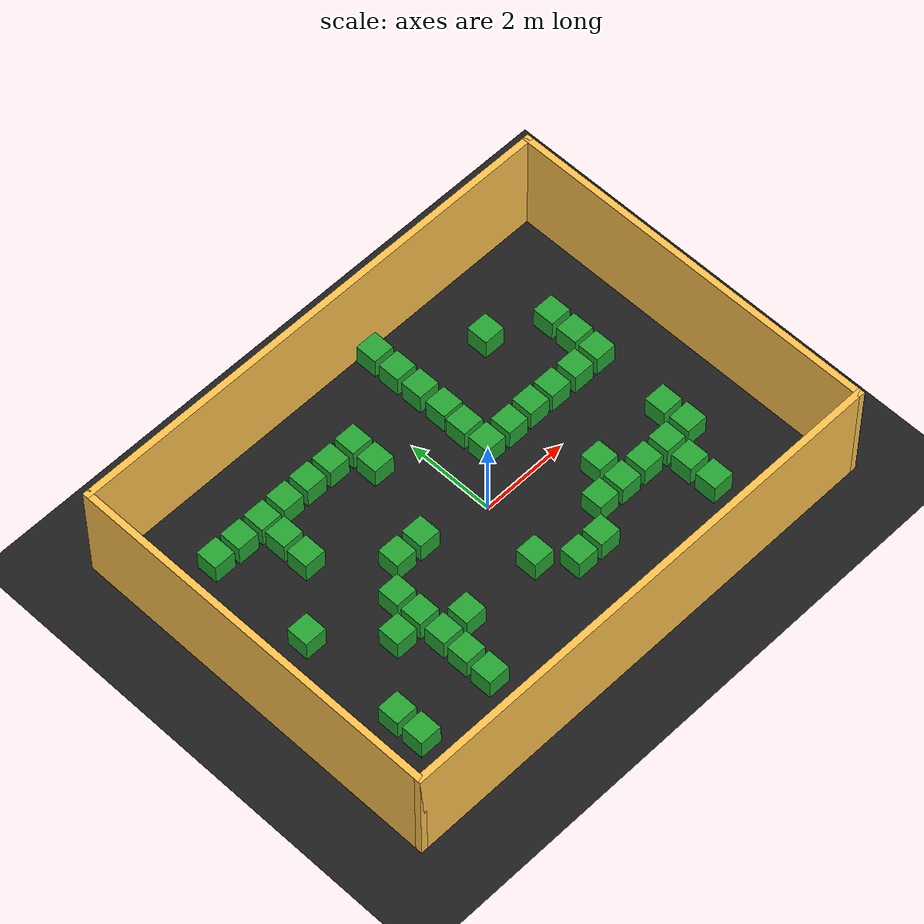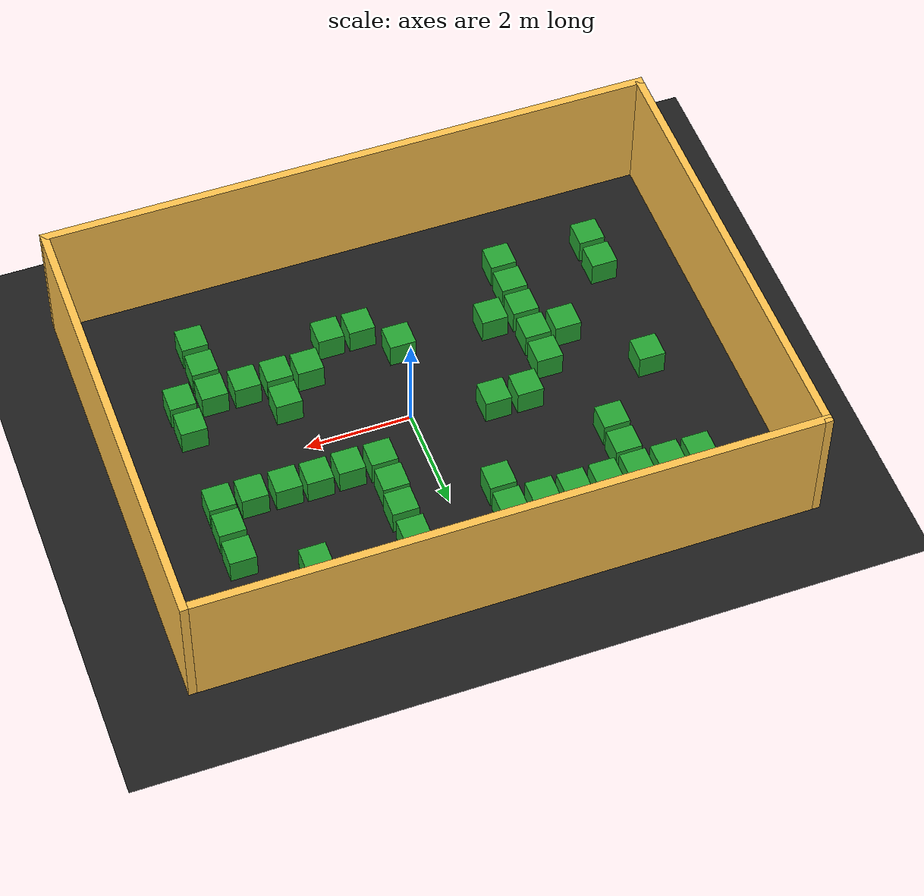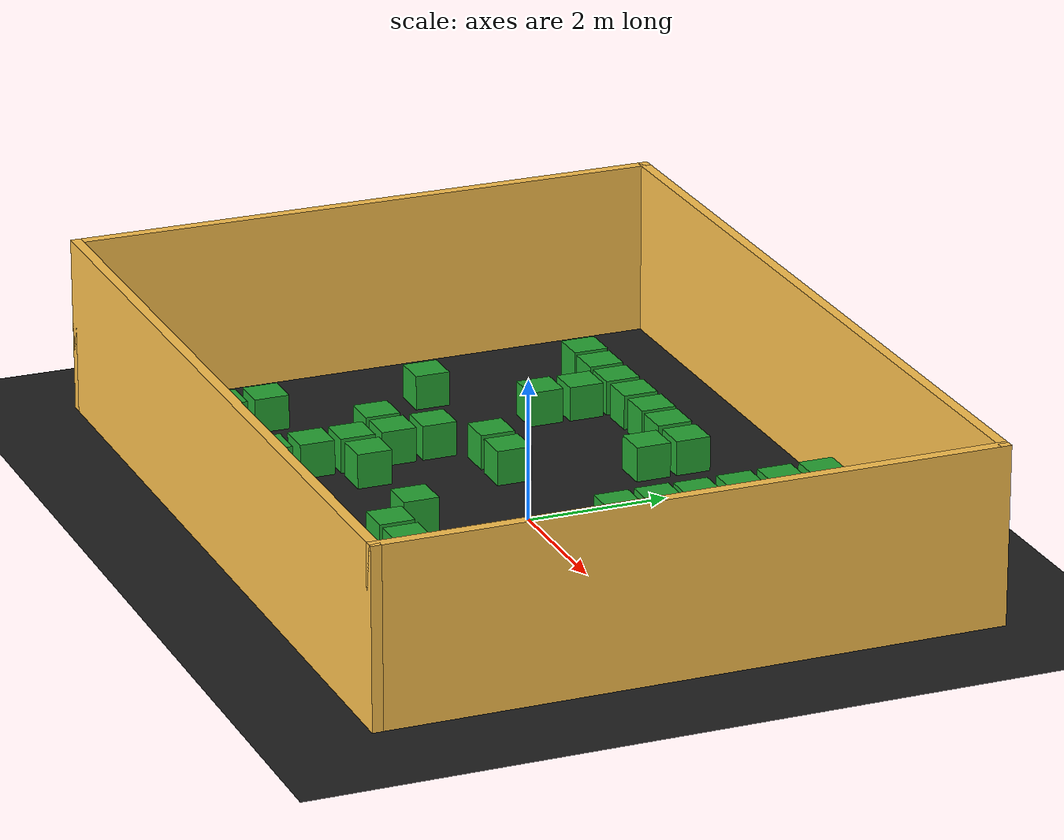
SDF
<sdf version="1.7">
 <world name="default">
  <light name="sun" type="directional">
   <pose>0 0 10 0 -0 0</pose>
   <diffuse>0.8 0.8 0.8 1</diffuse>
   <specular>0.2 0.2 0.2 1</specular>
   <attenuation>
    <range>1000</range>
    <constant>0.9</constant>
    <linear>0.01</linear>
    <quadratic>0.001</quadratic>
   </attenuation>
   <direction>-0.5 0.1 -0.9</direction>
   <spot><inner_angle>0</inner_angle><outer_angle>0</outer_angle><falloff>0</falloff></spot>
  </light>
  <model name="ground_plane">
   <static>1</static>
   <link name="link">
    <collision name="collision">
     <geometry><plane><normal>0 0 1</normal><size>100 100</size></plane></geometry>
     <surface>
      <friction>
       <ode>
        <mu>1.000000</mu>
        <mu2>1.000000</mu2>
        <fdir1>0.000000 0.000000 0.000000</fdir1>
        <slip1>0.000000</slip1>
        <slip2>0.000000</slip2>
       </ode>
      </friction>
      <bounce>
       <restitution_coefficient>0.000000</restitution_coefficient>
       <threshold>100000.000000</threshold>
      </bounce>
      <contact>
       <ode>
        <soft_cfm>0.000000</soft_cfm>
        <soft_erp>0.200000</soft_erp>
        <kp>1000000000.000000</kp>
        <kd>1.000000</kd>
        <max_vel>100.000000</max_vel>
        <min_depth>0.001000</min_depth>
       </ode>
      </contact>
     </surface>
    </collision>
    <visual name="visual">
     <cast_shadows>0</cast_shadows>
     <geometry><plane><normal>0 0 1</normal><size>100 100</size></plane></geometry>
     <material>
      <script><uri>file://media/materials/scripts/gazebo.material</uri><name>Gazebo/Black</name></script>
     </material>
    </visual>
   </link>
  </model>
  <gravity>0 0 -9.8</gravity>
  <magnetic_field>6e-06 2.3e-05 -4.2e-05</magnetic_field>
  <atmosphere type="adiabatic"/>
  <physics type="ode">
   <max_step_size>0.001</max_step_size>
   <real_time_factor>1</real_time_factor>
   <real_time_update_rate>1000</real_time_update_rate>
  </physics>
  <scene><ambient>0.4 0.4 0.4 1</ambient><background>0.7 0.7 0.7 1</background><shadows>1</shadows></scene>
  <spherical_coordinates>
   <surface_model>EARTH_WGS84</surface_model>
   <latitude_deg>0</latitude_deg>
   <longitude_deg>0</longitude_deg>
   <elevation>0</elevation>
   <heading_deg>0</heading_deg>
  </spherical_coordinates>
  <model name="aius3011">
   <pose>-0.3 0 0 0 -0 0</pose>
   <link name="Wall_0">
    <collision name="Wall_0_Collision">
     <geometry><box><size>11.7 0.15 2.5</size></box></geometry>
     <pose>0 0 1.25 0 -0 0</pose>
    </collision>
    <visual name="Wall_0_Visual">
     <pose>0 0 1.25 0 -0 0</pose>
     <geometry><box><size>11.7 0.15 2.5</size></box></geometry>
     <material>
      <script><uri>file://media/materials/scripts/gazebo.material</uri><name>Gazebo/Grey</name></script>
      <ambient>1 0.764706 0.305882 1</ambient>
     </material>
     <meta><layer>0</layer></meta>
    </visual>
    <pose>-0 -4.275 0 0 -0 0</pose>
   </link>
   <link name="Wall_2">
    <collision name="Wall_2_Collision">
     <geometry><box><size>8.7 0.15 2.5</size></box></geometry>
     <pose>0 0 1.25 0 -0 0</pose>
    </collision>
    <visual name="Wall_2_Visual">
     <pose>0 0 1.25 0 -0 0</pose>
     <geometry><box><size>8.7 0.15 2.5</size></box></geometry>
     <material>
      <script><uri>file://media/materials/scripts/gazebo.material</uri><name>Gazebo/Grey</name></script>
      <ambient>1 0.764706 0.305882 1</ambient>
     </material>
     <meta><layer>0</layer></meta>
    </visual>
    <pose>-5.775 0 0 0 -0 1.5708</pose>
   </link>
   <link name="Wall_4">
    <collision name="Wall_4_Collision">
     <geometry><box><size>11.7 0.15 2.5</size></box></geometry>
     <pose>0 0 1.25 0 -0 0</pose>
    </collision>
    <visual name="Wall_4_Visual">
     <pose>0 0 1.25 0 -0 0</pose>
     <geometry><box><size>11.7 0.15 2.5</size></box></geometry>
     <material>
      <script><uri>file://media/materials/scripts/gazebo.material</uri><name>Gazebo/Grey</name></script>
      <ambient>1 0.764706 0.305882 1</ambient>
     </material>
     <meta><layer>0</layer></meta>
    </visual>
    <pose>-0 4.275 0 0 -0 0</pose>
   </link>
   <link name="Wall_6">
    <collision name="Wall_6_Collision">
     <geometry><box><size>8.7 0.15 2.5</size></box></geometry>
     <pose>0 0 1.25 0 -0 0</pose>
    </collision>
    <visual name="Wall_6_Visual">
     <pose>0 0 1.25 0 -0 0</pose>
     <geometry><box><size>8.7 0.15 2.5</size></box></geometry>
     <material>
      <script><uri>file://media/materials/scripts/gazebo.material</uri><name>Gazebo/Grey</name></script>
      <ambient>1 0.764706 0.305882 1</ambient>
     </material>
     <meta><layer>0</layer></meta>
    </visual>
    <pose>5.775 0 0 0 -0 -1.5708</pose>
   </link>
   <static>1</static>
  </model>
  <model name="obstacle00">
   <link name="link_0">
    <inertial>
     <mass>0.1</mass>
     <inertia><ixx>10</ixx><ixy>0</ixy><ixz>0</ixz><iyy>10</iyy><iyz>0</iyz><izz>10</izz></inertia>
    </inertial>
    <visual name="visual">
     <geometry><box><size>0.5 0.5 0.5</size></box></geometry>
     <material>
      <lighting>1</lighting>
      <script><uri>file://media/materials/scripts/gazebo.material</uri><name>Gazebo/Green</name></script>
      <shader type="pixel"><normal_map>__default__</normal_map></shader>
      <ambient>0.3 0.3 0.3 1</ambient>
      <diffuse>0.7 0.7 0.7 1</diffuse>
      <specular>0.01 0.01 0.01 1</specular>
      <emissive>0 0 0 1</emissive>
     </material>
    </visual>
    <collision name="collision">
     <geometry><box><size>0.5 0.5 0.5</size></box></geometry>
     <surface>
      <friction>
       <ode>
        <mu>0.998500</mu>
        <mu2>0.998500</mu2>
        <fdir1>0.000000 0.000000 0.000000</fdir1>
        <slip1>0.000000</slip1>
        <slip2>0.000000</slip2>
       </ode>
      </friction>
      <bounce>
       <restitution_coefficient>0.000000</restitution_coefficient>
       <threshold>100000.000000</threshold>
      </bounce>
      <contact>
       <ode>
        <soft_cfm>0.000000</soft_cfm>
        <soft_erp>0.200000</soft_erp>
        <kp>100000.000000</kp>
        <kd>1.000000</kd>
        <max_vel>100.000000</max_vel>
        <min_depth>0.001000</min_depth>
       </ode>
      </contact>
     </surface>
     <laser_retro>0.000000</laser_retro>
    </collision>
   </link>
   <static>0</static>
   <pose>3.92032 2.10108 0.26 0 -0 0</pose>
  </model>
  <model name="obstacle01">
   <link name="link_0">
    <inertial>
     <mass>0.1</mass>
     <inertia><ixx>10</ixx><ixy>0</ixy><ixz>0</ixz><iyy>10</iyy><iyz>0</iyz><izz>10</izz></inertia>
    </inertial>
    <visual name="visual">
     <geometry><box><size>0.5 0.5 0.5</size></box></geometry>
     <material>
      <lighting>1</lighting>
      <script><uri>file://media/materials/scripts/gazebo.material</uri><name>Gazebo/Green</name></script>
      <shader type="pixel"><normal_map>__default__</normal_map></shader>
      <ambient>0.3 0.3 0.3 1</ambient>
      <diffuse>0.7 0.7 0.7 1</diffuse>
      <specular>0.01 0.01 0.01 1</specular>
      <emissive>0 0 0 1</emissive>
     </material>
    </visual>
    <collision name="collision">
     <geometry><box><size>0.5 0.5 0.5</size></box></geometry>
     <surface>
      <friction>
       <ode>
        <mu>0.998500</mu>
        <mu2>0.998500</mu2>
        <fdir1>0.000000 0.000000 0.000000</fdir1>
        <slip1>0.000000</slip1>
        <slip2>0.000000</slip2>
       </ode>
      </friction>
      <bounce>
       <restitution_coefficient>0.000000</restitution_coefficient>
       <threshold>100000.000000</threshold>
      </bounce>
      <contact>
       <ode>
        <soft_cfm>0.000000</soft_cfm>
        <soft_erp>0.200000</soft_erp>
        <kp>100000.000000</kp>
        <kd>1.000000</kd>
        <max_vel>100.000000</max_vel>
        <min_depth>0.001000</min_depth>
       </ode>
      </contact>
     </surface>
     <laser_retro>0.000000</laser_retro>
    </collision>
   </link>
   <static>0</static>
   <pose>3.91542 1.48158 0.26 0 -0 0</pose>
  </model>
  <model name="obstacle02">
   <link name="link_0">
    <inertial>
     <mass>0.1</mass>
     <inertia><ixx>10</ixx><ixy>0</ixy><ixz>0</ixz><iyy>10</iyy><iyz>0</iyz><izz>10</izz></inertia>
    </inertial>
    <visual name="visual">
     <geometry><box><size>0.5 0.5 0.5</size></box></geometry>
     <material>
      <lighting>1</lighting>
      <script><uri>file://media/materials/scripts/gazebo.material</uri><name>Gazebo/Green</name></script>
      <shader type="pixel"><normal_map>__default__</normal_map></shader>
      <ambient>0.3 0.3 0.3 1</ambient>
      <diffuse>0.7 0.7 0.7 1</diffuse>
      <specular>0.01 0.01 0.01 1</specular>
      <emissive>0 0 0 1</emissive>
     </material>
    </visual>
    <collision name="collision">
     <geometry><box><size>0.5 0.5 0.5</size></box></geometry>
     <surface>
      <friction>
       <ode>
        <mu>0.998500</mu>
        <mu2>0.998500</mu2>
        <fdir1>0.000000 0.000000 0.000000</fdir1>
        <slip1>0.000000</slip1>
        <slip2>0.000000</slip2>
       </ode>
      </friction>
      <bounce>
       <restitution_coefficient>0.000000</restitution_coefficient>
       <threshold>100000.000000</threshold>
      </bounce>
      <contact>
       <ode>
        <soft_cfm>0.000000</soft_cfm>
        <soft_erp>0.200000</soft_erp>
        <kp>100000.000000</kp>
        <kd>1.000000</kd>
        <max_vel>100.000000</max_vel>
        <min_depth>0.001000</min_depth>
       </ode>
      </contact>
     </surface>
     <laser_retro>0.000000</laser_retro>
    </collision>
   </link>
   <static>0</static>
   <pose>3.91543 0.897046 0.26 0 -0 0</pose>
  </model>
  <model name="obstacle03">
   <link name="link_0">
    <inertial>
     <mass>0.1</mass>
     <inertia><ixx>10</ixx><ixy>0</ixy><ixz>0</ixz><iyy>10</iyy><iyz>0</iyz><izz>10</izz></inertia>
    </inertial>
    <visual name="visual">
     <geometry><box><size>0.5 0.5 0.5</size></box></geometry>
     <material>
      <lighting>1</lighting>
      <script><uri>file://media/materials/scripts/gazebo.material</uri><name>Gazebo/Green</name></script>
      <shader type="pixel"><normal_map>__default__</normal_map></shader>
      <ambient>0.3 0.3 0.3 1</ambient>
      <diffuse>0.7 0.7 0.7 1</diffuse>
      <specular>0.01 0.01 0.01 1</specular>
      <emissive>0 0 0 1</emissive>
     </material>
    </visual>
    <collision name="collision">
     <geometry><box><size>0.5 0.5 0.5</size></box></geometry>
     <surface>
      <friction>
       <ode>
        <mu>0.998500</mu>
        <mu2>0.998500</mu2>
        <fdir1>0.000000 0.000000 0.000000</fdir1>
        <slip1>0.000000</slip1>
        <slip2>0.000000</slip2>
       </ode>
      </friction>
      <bounce>
       <restitution_coefficient>0.000000</restitution_coefficient>
       <threshold>100000.000000</threshold>
      </bounce>
      <contact>
       <ode>
        <soft_cfm>0.000000</soft_cfm>
        <soft_erp>0.200000</soft_erp>
        <kp>100000.000000</kp>
        <kd>1.000000</kd>
        <max_vel>100.000000</max_vel>
        <min_depth>0.001000</min_depth>
       </ode>
      </contact>
     </surface>
     <laser_retro>0.000000</laser_retro>
    </collision>
   </link>
   <static>0</static>
   <pose>3.3151 0.898305 0.26 0 -0 0</pose>
  </model>
  <model name="obstacle14">
   <link name="link_0">
    <inertial>
     <mass>0.1</mass>
     <inertia><ixx>10</ixx><ixy>0</ixy><ixz>0</ixz><iyy>10</iyy><iyz>0</iyz><izz>10</izz></inertia>
    </inertial>
    <visual name="visual">
     <geometry><box><size>0.5 0.5 0.5</size></box></geometry>
     <material>
      <lighting>1</lighting>
      <script><uri>file://media/materials/scripts/gazebo.material</uri><name>Gazebo/Green</name></script>
      <shader type="pixel"><normal_map>__default__</normal_map></shader>
      <ambient>0.3 0.3 0.3 1</ambient>
      <diffuse>0.7 0.7 0.7 1</diffuse>
      <specular>0.01 0.01 0.01 1</specular>
      <emissive>0 0 0 1</emissive>
     </material>
    </visual>
    <collision name="collision">
     <geometry><box><size>0.5 0.5 0.5</size></box></geometry>
     <surface>
      <friction>
       <ode>
        <mu>0.998500</mu>
        <mu2>0.998500</mu2>
        <fdir1>0.000000 0.000000 0.000000</fdir1>
        <slip1>0.000000</slip1>
        <slip2>0.000000</slip2>
       </ode>
      </friction>
      <bounce>
       <restitution_coefficient>0.000000</restitution_coefficient>
       <threshold>100000.000000</threshold>
      </bounce>
      <contact>
       <ode>
        <soft_cfm>0.000000</soft_cfm>
        <soft_erp>0.200000</soft_erp>
        <kp>100000.000000</kp>
        <kd>1.000000</kd>
        <max_vel>100.000000</max_vel>
        <min_depth>0.001000</min_depth>
       </ode>
      </contact>
     </surface>
     <laser_retro>0.000000</laser_retro>
    </collision>
   </link>
   <static>0</static>
   <pose>2.69199 0.910463 0.26 0 -0 0</pose>
  </model>
  <model name="obstacle25">
   <link name="link_0">
    <inertial>
     <mass>0.1</mass>
     <inertia><ixx>10</ixx><ixy>0</ixy><ixz>0</ixz><iyy>10</iyy><iyz>0</iyz><izz>10</izz></inertia>
    </inertial>
    <visual name="visual">
     <geometry><box><size>0.5 0.5 0.5</size></box></geometry>
     <material>
      <lighting>1</lighting>
      <script><uri>file://media/materials/scripts/gazebo.material</uri><name>Gazebo/Green</name></script>
      <shader type="pixel"><normal_map>__default__</normal_map></shader>
      <ambient>0.3 0.3 0.3 1</ambient>
      <diffuse>0.7 0.7 0.7 1</diffuse>
      <specular>0.01 0.01 0.01 1</specular>
      <emissive>0 0 0 1</emissive>
     </material>
    </visual>
    <collision name="collision">
     <geometry><box><size>0.5 0.5 0.5</size></box></geometry>
     <surface>
      <friction>
       <ode>
        <mu>0.998500</mu>
        <mu2>0.998500</mu2>
        <fdir1>0.000000 0.000000 0.000000</fdir1>
        <slip1>0.000000</slip1>
        <slip2>0.000000</slip2>
       </ode>
      </friction>
      <bounce>
       <restitution_coefficient>0.000000</restitution_coefficient>
       <threshold>100000.000000</threshold>
      </bounce>
      <contact>
       <ode>
        <soft_cfm>0.000000</soft_cfm>
        <soft_erp>0.200000</soft_erp>
        <kp>100000.000000</kp>
        <kd>1.000000</kd>
        <max_vel>100.000000</max_vel>
        <min_depth>0.001000</min_depth>
       </ode>
      </contact>
     </surface>
     <laser_retro>0.000000</laser_retro>
    </collision>
   </link>
   <static>0</static>
   <pose>2.11146 0.922356 0.26 0 -0 0</pose>
  </model>
  <model name="obstacle36">
   <link name="link_0">
    <inertial>
     <mass>0.1</mass>
     <inertia><ixx>10</ixx><ixy>0</ixy><ixz>0</ixz><iyy>10</iyy><iyz>0</iyz><izz>10</izz></inertia>
    </inertial>
    <visual name="visual">
     <geometry><box><size>0.5 0.5 0.5</size></box></geometry>
     <material>
      <lighting>1</lighting>
      <script><uri>file://media/materials/scripts/gazebo.material</uri><name>Gazebo/Green</name></script>
      <shader type="pixel"><normal_map>__default__</normal_map></shader>
      <ambient>0.3 0.3 0.3 1</ambient>
      <diffuse>0.7 0.7 0.7 1</diffuse>
      <specular>0.01 0.01 0.01 1</specular>
      <emissive>0 0 0 1</emissive>
     </material>
    </visual>
    <collision name="collision">
     <geometry><box><size>0.5 0.5 0.5</size></box></geometry>
     <surface>
      <friction>
       <ode>
        <mu>0.998500</mu>
        <mu2>0.998500</mu2>
        <fdir1>0.000000 0.000000 0.000000</fdir1>
        <slip1>0.000000</slip1>
        <slip2>0.000000</slip2>
       </ode>
      </friction>
      <bounce>
       <restitution_coefficient>0.000000</restitution_coefficient>
       <threshold>100000.000000</threshold>
      </bounce>
      <contact>
       <ode>
        <soft_cfm>0.000000</soft_cfm>
        <soft_erp>0.200000</soft_erp>
        <kp>100000.000000</kp>
        <kd>1.000000</kd>
        <max_vel>100.000000</max_vel>
        <min_depth>0.001000</min_depth>
       </ode>
      </contact>
     </surface>
     <laser_retro>0.000000</laser_retro>
    </collision>
   </link>
   <static>0</static>
   <pose>1.50877 0.902109 0.26 0 -0 0</pose>
  </model>
  <model name="obstacle43">
   <link name="link_0">
    <inertial>
     <mass>0.1</mass>
     <inertia><ixx>10</ixx><ixy>0</ixy><ixz>0</ixz><iyy>10</iyy><iyz>0</iyz><izz>10</izz></inertia>
    </inertial>
    <visual name="visual">
     <geometry><box><size>0.5 0.5 0.5</size></box></geometry>
     <material>
      <lighting>1</lighting>
      <script><uri>file://media/materials/scripts/gazebo.material</uri><name>Gazebo/Green</name></script>
      <shader type="pixel"><normal_map>__default__</normal_map></shader>
      <ambient>0.3 0.3 0.3 1</ambient>
      <diffuse>0.7 0.7 0.7 1</diffuse>
      <specular>0.01 0.01 0.01 1</specular>
      <emissive>0 0 0 1</emissive>
     </material>
    </visual>
    <collision name="collision">
     <geometry><box><size>0.5 0.5 0.5</size></box></geometry>
     <surface>
      <friction>
       <ode>
        <mu>0.998500</mu>
        <mu2>0.998500</mu2>
        <fdir1>0.000000 0.000000 0.000000</fdir1>
        <slip1>0.000000</slip1>
        <slip2>0.000000</slip2>
       </ode>
      </friction>
      <bounce>
       <restitution_coefficient>0.000000</restitution_coefficient>
       <threshold>100000.000000</threshold>
      </bounce>
      <contact>
       <ode>
        <soft_cfm>0.000000</soft_cfm>
        <soft_erp>0.200000</soft_erp>
        <kp>100000.000000</kp>
        <kd>1.000000</kd>
        <max_vel>100.000000</max_vel>
        <min_depth>0.001000</min_depth>
       </ode>
      </contact>
     </surface>
     <laser_retro>0.000000</laser_retro>
    </collision>
   </link>
   <static>0</static>
   <pose>0.90586 0.913955 0.26 0 -0 0</pose>
  </model>
  <model name="obstacle44">
   <link name="link_0">
    <inertial>
     <mass>0.1</mass>
     <inertia><ixx>10</ixx><ixy>0</ixy><ixz>0</ixz><iyy>10</iyy><iyz>0</iyz><izz>10</izz></inertia>
    </inertial>
    <visual name="visual">
     <geometry><box><size>0.5 0.5 0.5</size></box></geometry>
     <material>
      <lighting>1</lighting>
      <script><uri>file://media/materials/scripts/gazebo.material</uri><name>Gazebo/Green</name></script>
      <shader type="pixel"><normal_map>__default__</normal_map></shader>
      <ambient>0.3 0.3 0.3 1</ambient>
      <diffuse>0.7 0.7 0.7 1</diffuse>
      <specular>0.01 0.01 0.01 1</specular>
      <emissive>0 0 0 1</emissive>
     </material>
    </visual>
    <collision name="collision">
     <geometry><box><size>0.5 0.5 0.5</size></box></geometry>
     <surface>
      <friction>
       <ode>
        <mu>0.998500</mu>
        <mu2>0.998500</mu2>
        <fdir1>0.000000 0.000000 0.000000</fdir1>
        <slip1>0.000000</slip1>
        <slip2>0.000000</slip2>
       </ode>
      </friction>
      <bounce>
       <restitution_coefficient>0.000000</restitution_coefficient>
       <threshold>100000.000000</threshold>
      </bounce>
      <contact>
       <ode>
        <soft_cfm>0.000000</soft_cfm>
        <soft_erp>0.200000</soft_erp>
        <kp>100000.000000</kp>
        <kd>1.000000</kd>
        <max_vel>100.000000</max_vel>
        <min_depth>0.001000</min_depth>
       </ode>
      </contact>
     </surface>
     <laser_retro>0.000000</laser_retro>
    </collision>
   </link>
   <static>0</static>
   <pose>2.70939 2.70606 0.26 0 -0 0</pose>
  </model>
  <model name="obstacle45">
   <link name="link_0">
    <inertial>
     <mass>0.1</mass>
     <inertia><ixx>10</ixx><ixy>0</ixy><ixz>0</ixz><iyy>10</iyy><iyz>0</iyz><izz>10</izz></inertia>
    </inertial>
    <visual name="visual">
     <geometry><box><size>0.5 0.5 0.5</size></box></geometry>
     <material>
      <lighting>1</lighting>
      <script><uri>file://media/materials/scripts/gazebo.material</uri><name>Gazebo/Green</name></script>
      <shader type="pixel"><normal_map>__default__</normal_map></shader>
      <ambient>0.3 0.3 0.3 1</ambient>
      <diffuse>0.7 0.7 0.7 1</diffuse>
      <specular>0.01 0.01 0.01 1</specular>
      <emissive>0 0 0 1</emissive>
     </material>
    </visual>
    <collision name="collision">
     <geometry><box><size>0.5 0.5 0.5</size></box></geometry>
     <surface>
      <friction>
       <ode>
        <mu>0.998500</mu>
        <mu2>0.998500</mu2>
        <fdir1>0.000000 0.000000 0.000000</fdir1>
        <slip1>0.000000</slip1>
        <slip2>0.000000</slip2>
       </ode>
      </friction>
      <bounce>
       <restitution_coefficient>0.000000</restitution_coefficient>
       <threshold>100000.000000</threshold>
      </bounce>
      <contact>
       <ode>
        <soft_cfm>0.000000</soft_cfm>
        <soft_erp>0.200000</soft_erp>
        <kp>100000.000000</kp>
        <kd>1.000000</kd>
        <max_vel>100.000000</max_vel>
        <min_depth>0.001000</min_depth>
       </ode>
      </contact>
     </surface>
     <laser_retro>0.000000</laser_retro>
    </collision>
   </link>
   <static>0</static>
   <pose>0.893566 3.91336 0.26 0 -0 0</pose>
  </model>
  <model name="obstacle46">
   <link name="link_0">
    <inertial>
     <mass>0.1</mass>
     <inertia><ixx>10</ixx><ixy>0</ixy><ixz>0</ixz><iyy>10</iyy><iyz>0</iyz><izz>10</izz></inertia>
    </inertial>
    <visual name="visual">
     <geometry><box><size>0.5 0.5 0.5</size></box></geometry>
     <material>
      <lighting>1</lighting>
      <script><uri>file://media/materials/scripts/gazebo.material</uri><name>Gazebo/Green</name></script>
      <shader type="pixel"><normal_map>__default__</normal_map></shader>
      <ambient>0.3 0.3 0.3 1</ambient>
      <diffuse>0.7 0.7 0.7 1</diffuse>
      <specular>0.01 0.01 0.01 1</specular>
      <emissive>0 0 0 1</emissive>
     </material>
    </visual>
    <collision name="collision">
     <geometry><box><size>0.5 0.5 0.5</size></box></geometry>
     <surface>
      <friction>
       <ode>
        <mu>0.998500</mu>
        <mu2>0.998500</mu2>
        <fdir1>0.000000 0.000000 0.000000</fdir1>
        <slip1>0.000000</slip1>
        <slip2>0.000000</slip2>
       </ode>
      </friction>
      <bounce>
       <restitution_coefficient>0.000000</restitution_coefficient>
       <threshold>100000.000000</threshold>
      </bounce>
      <contact>
       <ode>
        <soft_cfm>0.000000</soft_cfm>
        <soft_erp>0.200000</soft_erp>
        <kp>100000.000000</kp>
        <kd>1.000000</kd>
        <max_vel>100.000000</max_vel>
        <min_depth>0.001000</min_depth>
       </ode>
      </contact>
     </surface>
     <laser_retro>0.000000</laser_retro>
    </collision>
   </link>
   <static>0</static>
   <pose>0.893569 3.30008 0.26 0 -0 0</pose>
  </model>
  <model name="obstacle47">
   <link name="link_0">
    <inertial>
     <mass>0.1</mass>
     <inertia><ixx>10</ixx><ixy>0</ixy><ixz>0</ixz><iyy>10</iyy><iyz>0</iyz><izz>10</izz></inertia>
    </inertial>
    <visual name="visual">
     <geometry><box><size>0.5 0.5 0.5</size></box></geometry>
     <material>
      <lighting>1</lighting>
      <script><uri>file://media/materials/scripts/gazebo.material</uri><name>Gazebo/Green</name></script>
      <shader type="pixel"><normal_map>__default__</normal_map></shader>
      <ambient>0.3 0.3 0.3 1</ambient>
      <diffuse>0.7 0.7 0.7 1</diffuse>
      <specular>0.01 0.01 0.01 1</specular>
      <emissive>0 0 0 1</emissive>
     </material>
    </visual>
    <collision name="collision">
     <geometry><box><size>0.5 0.5 0.5</size></box></geometry>
     <surface>
      <friction>
       <ode>
        <mu>0.998500</mu>
        <mu2>0.998500</mu2>
        <fdir1>0.000000 0.000000 0.000000</fdir1>
        <slip1>0.000000</slip1>
        <slip2>0.000000</slip2>
       </ode>
      </friction>
      <bounce>
       <restitution_coefficient>0.000000</restitution_coefficient>
       <threshold>100000.000000</threshold>
      </bounce>
      <contact>
       <ode>
        <soft_cfm>0.000000</soft_cfm>
        <soft_erp>0.200000</soft_erp>
        <kp>100000.000000</kp>
        <kd>1.000000</kd>
        <max_vel>100.000000</max_vel>
        <min_depth>0.001000</min_depth>
       </ode>
      </contact>
     </surface>
     <laser_retro>0.000000</laser_retro>
    </collision>
   </link>
   <static>0</static>
   <pose>0.904175 2.69756 0.26 0 -0 0</pose>
  </model>
  <model name="obstacle04">
   <link name="link_0">
    <inertial>
     <mass>0.1</mass>
     <inertia><ixx>10</ixx><ixy>0</ixy><ixz>0</ixz><iyy>10</iyy><iyz>0</iyz><izz>10</izz></inertia>
    </inertial>
    <visual name="visual">
     <geometry><box><size>0.5 0.5 0.5</size></box></geometry>
     <material>
      <lighting>1</lighting>
      <script><uri>file://media/materials/scripts/gazebo.material</uri><name>Gazebo/Green</name></script>
      <shader type="pixel"><normal_map>__default__</normal_map></shader>
      <ambient>0.3 0.3 0.3 1</ambient>
      <diffuse>0.7 0.7 0.7 1</diffuse>
      <specular>0.01 0.01 0.01 1</specular>
      <emissive>0 0 0 1</emissive>
     </material>
    </visual>
    <collision name="collision">
     <geometry><box><size>0.5 0.5 0.5</size></box></geometry>
     <surface>
      <friction>
       <ode>
        <mu>0.998500</mu>
        <mu2>0.998500</mu2>
        <fdir1>0.000000 0.000000 0.000000</fdir1>
        <slip1>0.000000</slip1>
        <slip2>0.000000</slip2>
       </ode>
      </friction>
      <bounce>
       <restitution_coefficient>0.000000</restitution_coefficient>
       <threshold>100000.000000</threshold>
      </bounce>
      <contact>
       <ode>
        <soft_cfm>0.000000</soft_cfm>
        <soft_erp>0.200000</soft_erp>
        <kp>100000.000000</kp>
        <kd>1.000000</kd>
        <max_vel>100.000000</max_vel>
        <min_depth>0.001000</min_depth>
       </ode>
      </contact>
     </surface>
     <laser_retro>0.000000</laser_retro>
    </collision>
   </link>
   <static>0</static>
   <pose>0.91478 2.06313 0.26 0 -0 0</pose>
  </model>
  <model name="obstacle05">
   <link name="link_0">
    <inertial>
     <mass>0.1</mass>
     <inertia><ixx>10</ixx><ixy>0</ixy><ixz>0</ixz><iyy>10</iyy><iyz>0</iyz><izz>10</izz></inertia>
    </inertial>
    <visual name="visual">
     <geometry><box><size>0.5 0.5 0.5</size></box></geometry>
     <material>
      <lighting>1</lighting>
      <script><uri>file://media/materials/scripts/gazebo.material</uri><name>Gazebo/Green</name></script>
      <shader type="pixel"><normal_map>__default__</normal_map></shader>
      <ambient>0.3 0.3 0.3 1</ambient>
      <diffuse>0.7 0.7 0.7 1</diffuse>
      <specular>0.01 0.01 0.01 1</specular>
      <emissive>0 0 0 1</emissive>
     </material>
    </visual>
    <collision name="collision">
     <geometry><box><size>0.5 0.5 0.5</size></box></geometry>
     <surface>
      <friction>
       <ode>
        <mu>0.998500</mu>
        <mu2>0.998500</mu2>
        <fdir1>0.000000 0.000000 0.000000</fdir1>
        <slip1>0.000000</slip1>
        <slip2>0.000000</slip2>
       </ode>
      </friction>
      <bounce>
       <restitution_coefficient>0.000000</restitution_coefficient>
       <threshold>100000.000000</threshold>
      </bounce>
      <contact>
       <ode>
        <soft_cfm>0.000000</soft_cfm>
        <soft_erp>0.200000</soft_erp>
        <kp>100000.000000</kp>
        <kd>1.000000</kd>
        <max_vel>100.000000</max_vel>
        <min_depth>0.001000</min_depth>
       </ode>
      </contact>
     </surface>
     <laser_retro>0.000000</laser_retro>
    </collision>
   </link>
   <static>0</static>
   <pose>0.893579 1.50256 0.26 0 -0 0</pose>
  </model>
  <model name="obstacle06">
   <link name="link_0">
    <inertial>
     <mass>0.1</mass>
     <inertia><ixx>10</ixx><ixy>0</ixy><ixz>0</ixz><iyy>10</iyy><iyz>0</iyz><izz>10</izz></inertia>
    </inertial>
    <visual name="visual">
     <geometry><box><size>0.5 0.5 0.5</size></box></geometry>
     <material>
      <lighting>1</lighting>
      <script><uri>file://media/materials/scripts/gazebo.material</uri><name>Gazebo/Green</name></script>
      <shader type="pixel"><normal_map>__default__</normal_map></shader>
      <ambient>0.3 0.3 0.3 1</ambient>
      <diffuse>0.7 0.7 0.7 1</diffuse>
      <specular>0.01 0.01 0.01 1</specular>
      <emissive>0 0 0 1</emissive>
     </material>
    </visual>
    <collision name="collision">
     <geometry><box><size>0.5 0.5 0.5</size></box></geometry>
     <surface>
      <friction>
       <ode>
        <mu>0.998500</mu>
        <mu2>0.998500</mu2>
        <fdir1>0.000000 0.000000 0.000000</fdir1>
        <slip1>0.000000</slip1>
        <slip2>0.000000</slip2>
       </ode>
      </friction>
      <bounce>
       <restitution_coefficient>0.000000</restitution_coefficient>
       <threshold>100000.000000</threshold>
      </bounce>
      <contact>
       <ode>
        <soft_cfm>0.000000</soft_cfm>
        <soft_erp>0.200000</soft_erp>
        <kp>100000.000000</kp>
        <kd>1.000000</kd>
        <max_vel>100.000000</max_vel>
        <min_depth>0.001000</min_depth>
       </ode>
      </contact>
     </surface>
     <laser_retro>0.000000</laser_retro>
    </collision>
   </link>
   <static>0</static>
   <pose>3.89608 -0.884451 0.26 0 -0 0</pose>
  </model>
  <model name="obstacle07">
   <link name="link_0">
    <inertial>
     <mass>0.1</mass>
     <inertia><ixx>10</ixx><ixy>0</ixy><ixz>0</ixz><iyy>10</iyy><iyz>0</iyz><izz>10</izz></inertia>
    </inertial>
    <visual name="visual">
     <geometry><box><size>0.5 0.5 0.5</size></box></geometry>
     <material>
      <lighting>1</lighting>
      <script><uri>file://media/materials/scripts/gazebo.material</uri><name>Gazebo/Green</name></script>
      <shader type="pixel"><normal_map>__default__</normal_map></shader>
      <ambient>0.3 0.3 0.3 1</ambient>
      <diffuse>0.7 0.7 0.7 1</diffuse>
      <specular>0.01 0.01 0.01 1</specular>
      <emissive>0 0 0 1</emissive>
     </material>
    </visual>
    <collision name="collision">
     <geometry><box><size>0.5 0.5 0.5</size></box></geometry>
     <surface>
      <friction>
       <ode>
        <mu>0.998500</mu>
        <mu2>0.998500</mu2>
        <fdir1>0.000000 0.000000 0.000000</fdir1>
        <slip1>0.000000</slip1>
        <slip2>0.000000</slip2>
       </ode>
      </friction>
      <bounce>
       <restitution_coefficient>0.000000</restitution_coefficient>
       <threshold>100000.000000</threshold>
      </bounce>
      <contact>
       <ode>
        <soft_cfm>0.000000</soft_cfm>
        <soft_erp>0.200000</soft_erp>
        <kp>100000.000000</kp>
        <kd>1.000000</kd>
        <max_vel>100.000000</max_vel>
        <min_depth>0.001000</min_depth>
       </ode>
      </contact>
     </surface>
     <laser_retro>0.000000</laser_retro>
    </collision>
   </link>
   <static>0</static>
   <pose>3.91632 -1.49502 0.26 0 -0 0</pose>
  </model>
  <model name="obstacle08">
   <link name="link_0">
    <inertial>
     <mass>0.1</mass>
     <inertia><ixx>10</ixx><ixy>0</ixy><ixz>0</ixz><iyy>10</iyy><iyz>0</iyz><izz>10</izz></inertia>
    </inertial>
    <visual name="visual">
     <geometry><box><size>0.5 0.5 0.5</size></box></geometry>
     <material>
      <lighting>1</lighting>
      <script><uri>file://media/materials/scripts/gazebo.material</uri><name>Gazebo/Green</name></script>
      <shader type="pixel"><normal_map>__default__</normal_map></shader>
      <ambient>0.3 0.3 0.3 1</ambient>
      <diffuse>0.7 0.7 0.7 1</diffuse>
      <specular>0.01 0.01 0.01 1</specular>
      <emissive>0 0 0 1</emissive>
     </material>
    </visual>
    <collision name="collision">
     <geometry><box><size>0.5 0.5 0.5</size></box></geometry>
     <surface>
      <friction>
       <ode>
        <mu>0.998500</mu>
        <mu2>0.998500</mu2>
        <fdir1>0.000000 0.000000 0.000000</fdir1>
        <slip1>0.000000</slip1>
        <slip2>0.000000</slip2>
       </ode>
      </friction>
      <bounce>
       <restitution_coefficient>0.000000</restitution_coefficient>
       <threshold>100000.000000</threshold>
      </bounce>
      <contact>
       <ode>
        <soft_cfm>0.000000</soft_cfm>
        <soft_erp>0.200000</soft_erp>
        <kp>100000.000000</kp>
        <kd>1.000000</kd>
        <max_vel>100.000000</max_vel>
        <min_depth>0.001000</min_depth>
       </ode>
      </contact>
     </surface>
     <laser_retro>0.000000</laser_retro>
    </collision>
   </link>
   <static>0</static>
   <pose>3.30564 -1.52303 0.26 0 -0 0</pose>
  </model>
  <model name="obstacle09">
   <link name="link_0">
    <inertial>
     <mass>0.1</mass>
     <inertia><ixx>10</ixx><ixy>0</ixy><ixz>0</ixz><iyy>10</iyy><iyz>0</iyz><izz>10</izz></inertia>
    </inertial>
    <visual name="visual">
     <geometry><box><size>0.5 0.5 0.5</size></box></geometry>
     <material>
      <lighting>1</lighting>
      <script><uri>file://media/materials/scripts/gazebo.material</uri><name>Gazebo/Green</name></script>
      <shader type="pixel"><normal_map>__default__</normal_map></shader>
      <ambient>0.3 0.3 0.3 1</ambient>
      <diffuse>0.7 0.7 0.7 1</diffuse>
      <specular>0.01 0.01 0.01 1</specular>
      <emissive>0 0 0 1</emissive>
     </material>
    </visual>
    <collision name="collision">
     <geometry><box><size>0.5 0.5 0.5</size></box></geometry>
     <surface>
      <friction>
       <ode>
        <mu>0.998500</mu>
        <mu2>0.998500</mu2>
        <fdir1>0.000000 0.000000 0.000000</fdir1>
        <slip1>0.000000</slip1>
        <slip2>0.000000</slip2>
       </ode>
      </friction>
      <bounce>
       <restitution_coefficient>0.000000</restitution_coefficient>
       <threshold>100000.000000</threshold>
      </bounce>
      <contact>
       <ode>
        <soft_cfm>0.000000</soft_cfm>
        <soft_erp>0.200000</soft_erp>
        <kp>100000.000000</kp>
        <kd>1.000000</kd>
        <max_vel>100.000000</max_vel>
        <min_depth>0.001000</min_depth>
       </ode>
      </contact>
     </surface>
     <laser_retro>0.000000</laser_retro>
    </collision>
   </link>
   <static>0</static>
   <pose>3.30776 -2.11794 0.26 0 -0 0</pose>
  </model>
  <model name="obstacle10">
   <link name="link_0">
    <inertial>
     <mass>0.1</mass>
     <inertia><ixx>10</ixx><ixy>0</ixy><ixz>0</ixz><iyy>10</iyy><iyz>0</iyz><izz>10</izz></inertia>
    </inertial>
    <visual name="visual">
     <geometry><box><size>0.5 0.5 0.5</size></box></geometry>
     <material>
      <lighting>1</lighting>
      <script><uri>file://media/materials/scripts/gazebo.material</uri><name>Gazebo/Green</name></script>
      <shader type="pixel"><normal_map>__default__</normal_map></shader>
      <ambient>0.3 0.3 0.3 1</ambient>
      <diffuse>0.7 0.7 0.7 1</diffuse>
      <specular>0.01 0.01 0.01 1</specular>
      <emissive>0 0 0 1</emissive>
     </material>
    </visual>
    <collision name="collision">
     <geometry><box><size>0.5 0.5 0.5</size></box></geometry>
     <surface>
      <friction>
       <ode>
        <mu>0.998500</mu>
        <mu2>0.998500</mu2>
        <fdir1>0.000000 0.000000 0.000000</fdir1>
        <slip1>0.000000</slip1>
        <slip2>0.000000</slip2>
       </ode>
      </friction>
      <bounce>
       <restitution_coefficient>0.000000</restitution_coefficient>
       <threshold>100000.000000</threshold>
      </bounce>
      <contact>
       <ode>
        <soft_cfm>0.000000</soft_cfm>
        <soft_erp>0.200000</soft_erp>
        <kp>100000.000000</kp>
        <kd>1.000000</kd>
        <max_vel>100.000000</max_vel>
        <min_depth>0.001000</min_depth>
       </ode>
      </contact>
     </surface>
     <laser_retro>0.000000</laser_retro>
    </collision>
   </link>
   <static>0</static>
   <pose>3.3121 -2.73775 0.26 0 -0 0</pose>
  </model>
  <model name="obstacle11">
   <link name="link_0">
    <inertial>
     <mass>0.1</mass>
     <inertia><ixx>10</ixx><ixy>0</ixy><ixz>0</ixz><iyy>10</iyy><iyz>0</iyz><izz>10</izz></inertia>
    </inertial>
    <visual name="visual">
     <geometry><box><size>0.5 0.5 0.5</size></box></geometry>
     <material>
      <lighting>1</lighting>
      <script><uri>file://media/materials/scripts/gazebo.material</uri><name>Gazebo/Green</name></script>
      <shader type="pixel"><normal_map>__default__</normal_map></shader>
      <ambient>0.3 0.3 0.3 1</ambient>
      <diffuse>0.7 0.7 0.7 1</diffuse>
      <specular>0.01 0.01 0.01 1</specular>
      <emissive>0 0 0 1</emissive>
     </material>
    </visual>
    <collision name="collision">
     <geometry><box><size>0.5 0.5 0.5</size></box></geometry>
     <surface>
      <friction>
       <ode>
        <mu>0.998500</mu>
        <mu2>0.998500</mu2>
        <fdir1>0.000000 0.000000 0.000000</fdir1>
        <slip1>0.000000</slip1>
        <slip2>0.000000</slip2>
       </ode>
      </friction>
      <bounce>
       <restitution_coefficient>0.000000</restitution_coefficient>
       <threshold>100000.000000</threshold>
      </bounce>
      <contact>
       <ode>
        <soft_cfm>0.000000</soft_cfm>
        <soft_erp>0.200000</soft_erp>
        <kp>100000.000000</kp>
        <kd>1.000000</kd>
        <max_vel>100.000000</max_vel>
        <min_depth>0.001000</min_depth>
       </ode>
      </contact>
     </surface>
     <laser_retro>0.000000</laser_retro>
    </collision>
   </link>
   <static>0</static>
   <pose>2.68317 -1.51911 0.26 0 -0 0</pose>
  </model>
  <model name="obstacle12">
   <link name="link_0">
    <inertial>
     <mass>0.1</mass>
     <inertia><ixx>10</ixx><ixy>0</ixy><ixz>0</ixz><iyy>10</iyy><iyz>0</iyz><izz>10</izz></inertia>
    </inertial>
    <visual name="visual">
     <geometry><box><size>0.5 0.5 0.5</size></box></geometry>
     <material>
      <lighting>1</lighting>
      <script><uri>file://media/materials/scripts/gazebo.material</uri><name>Gazebo/Green</name></script>
      <shader type="pixel"><normal_map>__default__</normal_map></shader>
      <ambient>0.3 0.3 0.3 1</ambient>
      <diffuse>0.7 0.7 0.7 1</diffuse>
      <specular>0.01 0.01 0.01 1</specular>
      <emissive>0 0 0 1</emissive>
     </material>
    </visual>
    <collision name="collision">
     <geometry><box><size>0.5 0.5 0.5</size></box></geometry>
     <surface>
      <friction>
       <ode>
        <mu>0.998500</mu>
        <mu2>0.998500</mu2>
        <fdir1>0.000000 0.000000 0.000000</fdir1>
        <slip1>0.000000</slip1>
        <slip2>0.000000</slip2>
       </ode>
      </friction>
      <bounce>
       <restitution_coefficient>0.000000</restitution_coefficient>
       <threshold>100000.000000</threshold>
      </bounce>
      <contact>
       <ode>
        <soft_cfm>0.000000</soft_cfm>
        <soft_erp>0.200000</soft_erp>
        <kp>100000.000000</kp>
        <kd>1.000000</kd>
        <max_vel>100.000000</max_vel>
        <min_depth>0.001000</min_depth>
       </ode>
      </contact>
     </surface>
     <laser_retro>0.000000</laser_retro>
    </collision>
   </link>
   <static>0</static>
   <pose>2.07189 -1.52285 0.26 0 -0 0</pose>
  </model>
  <model name="obstacle13">
   <link name="link_0">
    <inertial>
     <mass>0.1</mass>
     <inertia><ixx>10</ixx><ixy>0</ixy><ixz>0</ixz><iyy>10</iyy><iyz>0</iyz><izz>10</izz></inertia>
    </inertial>
    <visual name="visual">
     <geometry><box><size>0.5 0.5 0.5</size></box></geometry>
     <material>
      <lighting>1</lighting>
      <script><uri>file://media/materials/scripts/gazebo.material</uri><name>Gazebo/Green</name></script>
      <shader type="pixel"><normal_map>__default__</normal_map></shader>
      <ambient>0.3 0.3 0.3 1</ambient>
      <diffuse>0.7 0.7 0.7 1</diffuse>
      <specular>0.01 0.01 0.01 1</specular>
      <emissive>0 0 0 1</emissive>
     </material>
    </visual>
    <collision name="collision">
     <geometry><box><size>0.5 0.5 0.5</size></box></geometry>
     <surface>
      <friction>
       <ode>
        <mu>0.998500</mu>
        <mu2>0.998500</mu2>
        <fdir1>0.000000 0.000000 0.000000</fdir1>
        <slip1>0.000000</slip1>
        <slip2>0.000000</slip2>
       </ode>
      </friction>
      <bounce>
       <restitution_coefficient>0.000000</restitution_coefficient>
       <threshold>100000.000000</threshold>
      </bounce>
      <contact>
       <ode>
        <soft_cfm>0.000000</soft_cfm>
        <soft_erp>0.200000</soft_erp>
        <kp>100000.000000</kp>
        <kd>1.000000</kd>
        <max_vel>100.000000</max_vel>
        <min_depth>0.001000</min_depth>
       </ode>
      </contact>
     </surface>
     <laser_retro>0.000000</laser_retro>
    </collision>
   </link>
   <static>0</static>
   <pose>1.48581 -1.50282 0.26 0 -0 0</pose>
  </model>
  <model name="obstacle15">
   <link name="link_0">
    <inertial>
     <mass>0.1</mass>
     <inertia><ixx>10</ixx><ixy>0</ixy><ixz>0</ixz><iyy>10</iyy><iyz>0</iyz><izz>10</izz></inertia>
    </inertial>
    <visual name="visual">
     <geometry><box><size>0.5 0.5 0.5</size></box></geometry>
     <material>
      <lighting>1</lighting>
      <script><uri>file://media/materials/scripts/gazebo.material</uri><name>Gazebo/Green</name></script>
      <shader type="pixel"><normal_map>__default__</normal_map></shader>
      <ambient>0.3 0.3 0.3 1</ambient>
      <diffuse>0.7 0.7 0.7 1</diffuse>
      <specular>0.01 0.01 0.01 1</specular>
      <emissive>0 0 0 1</emissive>
     </material>
    </visual>
    <collision name="collision">
     <geometry><box><size>0.5 0.5 0.5</size></box></geometry>
     <surface>
      <friction>
       <ode>
        <mu>0.998500</mu>
        <mu2>0.998500</mu2>
        <fdir1>0.000000 0.000000 0.000000</fdir1>
        <slip1>0.000000</slip1>
        <slip2>0.000000</slip2>
       </ode>
      </friction>
      <bounce>
       <restitution_coefficient>0.000000</restitution_coefficient>
       <threshold>100000.000000</threshold>
      </bounce>
      <contact>
       <ode>
        <soft_cfm>0.000000</soft_cfm>
        <soft_erp>0.200000</soft_erp>
        <kp>100000.000000</kp>
        <kd>1.000000</kd>
        <max_vel>100.000000</max_vel>
        <min_depth>0.001000</min_depth>
       </ode>
      </contact>
     </surface>
     <laser_retro>0.000000</laser_retro>
    </collision>
   </link>
   <static>0</static>
   <pose>2.09475 -0.904872 0.26 0 -0 0</pose>
  </model>
  <model name="obstacle16">
   <link name="link_0">
    <inertial>
     <mass>0.1</mass>
     <inertia><ixx>10</ixx><ixy>0</ixy><ixz>0</ixz><iyy>10</iyy><iyz>0</iyz><izz>10</izz></inertia>
    </inertial>
    <visual name="visual">
     <geometry><box><size>0.5 0.5 0.5</size></box></geometry>
     <material>
      <lighting>1</lighting>
      <script><uri>file://media/materials/scripts/gazebo.material</uri><name>Gazebo/Green</name></script>
      <shader type="pixel"><normal_map>__default__</normal_map></shader>
      <ambient>0.3 0.3 0.3 1</ambient>
      <diffuse>0.7 0.7 0.7 1</diffuse>
      <specular>0.01 0.01 0.01 1</specular>
      <emissive>0 0 0 1</emissive>
     </material>
    </visual>
    <collision name="collision">
     <geometry><box><size>0.5 0.5 0.5</size></box></geometry>
     <surface>
      <friction>
       <ode>
        <mu>0.998500</mu>
        <mu2>0.998500</mu2>
        <fdir1>0.000000 0.000000 0.000000</fdir1>
        <slip1>0.000000</slip1>
        <slip2>0.000000</slip2>
       </ode>
      </friction>
      <bounce>
       <restitution_coefficient>0.000000</restitution_coefficient>
       <threshold>100000.000000</threshold>
      </bounce>
      <contact>
       <ode>
        <soft_cfm>0.000000</soft_cfm>
        <soft_erp>0.200000</soft_erp>
        <kp>100000.000000</kp>
        <kd>1.000000</kd>
        <max_vel>100.000000</max_vel>
        <min_depth>0.001000</min_depth>
       </ode>
      </contact>
     </surface>
     <laser_retro>0.000000</laser_retro>
    </collision>
   </link>
   <static>0</static>
   <pose>0.899255 -2.08804 0.26 0 -0 0</pose>
  </model>
  <model name="obstacle17">
   <link name="link_0">
    <inertial>
     <mass>0.1</mass>
     <inertia><ixx>10</ixx><ixy>0</ixy><ixz>0</ixz><iyy>10</iyy><iyz>0</iyz><izz>10</izz></inertia>
    </inertial>
    <visual name="visual">
     <geometry><box><size>0.5 0.5 0.5</size></box></geometry>
     <material>
      <lighting>1</lighting>
      <script><uri>file://media/materials/scripts/gazebo.material</uri><name>Gazebo/Green</name></script>
      <shader type="pixel"><normal_map>__default__</normal_map></shader>
      <ambient>0.3 0.3 0.3 1</ambient>
      <diffuse>0.7 0.7 0.7 1</diffuse>
      <specular>0.01 0.01 0.01 1</specular>
      <emissive>0 0 0 1</emissive>
     </material>
    </visual>
    <collision name="collision">
     <geometry><box><size>0.5 0.5 0.5</size></box></geometry>
     <surface>
      <friction>
       <ode>
        <mu>0.998500</mu>
        <mu2>0.998500</mu2>
        <fdir1>0.000000 0.000000 0.000000</fdir1>
        <slip1>0.000000</slip1>
        <slip2>0.000000</slip2>
       </ode>
      </friction>
      <bounce>
       <restitution_coefficient>0.000000</restitution_coefficient>
       <threshold>100000.000000</threshold>
      </bounce>
      <contact>
       <ode>
        <soft_cfm>0.000000</soft_cfm>
        <soft_erp>0.200000</soft_erp>
        <kp>100000.000000</kp>
        <kd>1.000000</kd>
        <max_vel>100.000000</max_vel>
        <min_depth>0.001000</min_depth>
       </ode>
      </contact>
     </surface>
     <laser_retro>0.000000</laser_retro>
    </collision>
   </link>
   <static>0</static>
   <pose>0.297209 -2.09079 0.26 0 -0 0</pose>
  </model>
  <model name="obstacle18">
   <link name="link_0">
    <inertial>
     <mass>0.1</mass>
     <inertia><ixx>10</ixx><ixy>0</ixy><ixz>0</ixz><iyy>10</iyy><iyz>0</iyz><izz>10</izz></inertia>
    </inertial>
    <visual name="visual">
     <geometry><box><size>0.5 0.5 0.5</size></box></geometry>
     <material>
      <lighting>1</lighting>
      <script><uri>file://media/materials/scripts/gazebo.material</uri><name>Gazebo/Green</name></script>
      <shader type="pixel"><normal_map>__default__</normal_map></shader>
      <ambient>0.3 0.3 0.3 1</ambient>
      <diffuse>0.7 0.7 0.7 1</diffuse>
      <specular>0.01 0.01 0.01 1</specular>
      <emissive>0 0 0 1</emissive>
     </material>
    </visual>
    <collision name="collision">
     <geometry><box><size>0.5 0.5 0.5</size></box></geometry>
     <surface>
      <friction>
       <ode>
        <mu>0.998500</mu>
        <mu2>0.998500</mu2>
        <fdir1>0.000000 0.000000 0.000000</fdir1>
        <slip1>0.000000</slip1>
        <slip2>0.000000</slip2>
       </ode>
      </friction>
      <bounce>
       <restitution_coefficient>0.000000</restitution_coefficient>
       <threshold>100000.000000</threshold>
      </bounce>
      <contact>
       <ode>
        <soft_cfm>0.000000</soft_cfm>
        <soft_erp>0.200000</soft_erp>
        <kp>100000.000000</kp>
        <kd>1.000000</kd>
        <max_vel>100.000000</max_vel>
        <min_depth>0.001000</min_depth>
       </ode>
      </contact>
     </surface>
     <laser_retro>0.000000</laser_retro>
    </collision>
   </link>
   <static>0</static>
   <pose>-0.296477 -1.51677 0.26 0 -0 0</pose>
  </model>
  <model name="obstacle19">
   <link name="link_0">
    <inertial>
     <mass>0.1</mass>
     <inertia><ixx>10</ixx><ixy>0</ixy><ixz>0</ixz><iyy>10</iyy><iyz>0</iyz><izz>10</izz></inertia>
    </inertial>
    <visual name="visual">
     <geometry><box><size>0.5 0.5 0.5</size></box></geometry>
     <material>
      <lighting>1</lighting>
      <script><uri>file://media/materials/scripts/gazebo.material</uri><name>Gazebo/Green</name></script>
      <shader type="pixel"><normal_map>__default__</normal_map></shader>
      <ambient>0.3 0.3 0.3 1</ambient>
      <diffuse>0.7 0.7 0.7 1</diffuse>
      <specular>0.01 0.01 0.01 1</specular>
      <emissive>0 0 0 1</emissive>
     </material>
    </visual>
    <collision name="collision">
     <geometry><box><size>0.5 0.5 0.5</size></box></geometry>
     <surface>
      <friction>
       <ode>
        <mu>0.998500</mu>
        <mu2>0.998500</mu2>
        <fdir1>0.000000 0.000000 0.000000</fdir1>
        <slip1>0.000000</slip1>
        <slip2>0.000000</slip2>
       </ode>
      </friction>
      <bounce>
       <restitution_coefficient>0.000000</restitution_coefficient>
       <threshold>100000.000000</threshold>
      </bounce>
      <contact>
       <ode>
        <soft_cfm>0.000000</soft_cfm>
        <soft_erp>0.200000</soft_erp>
        <kp>100000.000000</kp>
        <kd>1.000000</kd>
        <max_vel>100.000000</max_vel>
        <min_depth>0.001000</min_depth>
       </ode>
      </contact>
     </surface>
     <laser_retro>0.000000</laser_retro>
    </collision>
   </link>
   <static>0</static>
   <pose>-0.901554 2.6911 0.26 0 -0 0</pose>
  </model>
  <model name="obstacle20">
   <link name="link_0">
    <inertial>
     <mass>0.1</mass>
     <inertia><ixx>10</ixx><ixy>0</ixy><ixz>0</ixz><iyy>10</iyy><iyz>0</iyz><izz>10</izz></inertia>
    </inertial>
    <visual name="visual">
     <geometry><box><size>0.5 0.5 0.5</size></box></geometry>
     <material>
      <lighting>1</lighting>
      <script><uri>file://media/materials/scripts/gazebo.material</uri><name>Gazebo/Green</name></script>
      <shader type="pixel"><normal_map>__default__</normal_map></shader>
      <ambient>0.3 0.3 0.3 1</ambient>
      <diffuse>0.7 0.7 0.7 1</diffuse>
      <specular>0.01 0.01 0.01 1</specular>
      <emissive>0 0 0 1</emissive>
     </material>
    </visual>
    <collision name="collision">
     <geometry><box><size>0.5 0.5 0.5</size></box></geometry>
     <surface>
      <friction>
       <ode>
        <mu>0.998500</mu>
        <mu2>0.998500</mu2>
        <fdir1>0.000000 0.000000 0.000000</fdir1>
        <slip1>0.000000</slip1>
        <slip2>0.000000</slip2>
       </ode>
      </friction>
      <bounce>
       <restitution_coefficient>0.000000</restitution_coefficient>
       <threshold>100000.000000</threshold>
      </bounce>
      <contact>
       <ode>
        <soft_cfm>0.000000</soft_cfm>
        <soft_erp>0.200000</soft_erp>
        <kp>100000.000000</kp>
        <kd>1.000000</kd>
        <max_vel>100.000000</max_vel>
        <min_depth>0.001000</min_depth>
       </ode>
      </contact>
     </surface>
     <laser_retro>0.000000</laser_retro>
    </collision>
   </link>
   <static>0</static>
   <pose>-0.898111 2.10192 0.26 0 -0 0</pose>
  </model>
  <model name="obstacle21">
   <link name="link_0">
    <inertial>
     <mass>0.1</mass>
     <inertia><ixx>10</ixx><ixy>0</ixy><ixz>0</ixz><iyy>10</iyy><iyz>0</iyz><izz>10</izz></inertia>
    </inertial>
    <visual name="visual">
     <geometry><box><size>0.5 0.5 0.5</size></box></geometry>
     <material>
      <lighting>1</lighting>
      <script><uri>file://media/materials/scripts/gazebo.material</uri><name>Gazebo/Green</name></script>
      <shader type="pixel"><normal_map>__default__</normal_map></shader>
      <ambient>0.3 0.3 0.3 1</ambient>
      <diffuse>0.7 0.7 0.7 1</diffuse>
      <specular>0.01 0.01 0.01 1</specular>
      <emissive>0 0 0 1</emissive>
     </material>
    </visual>
    <collision name="collision">
     <geometry><box><size>0.5 0.5 0.5</size></box></geometry>
     <surface>
      <friction>
       <ode>
        <mu>0.998500</mu>
        <mu2>0.998500</mu2>
        <fdir1>0.000000 0.000000 0.000000</fdir1>
        <slip1>0.000000</slip1>
        <slip2>0.000000</slip2>
       </ode>
      </friction>
      <bounce>
       <restitution_coefficient>0.000000</restitution_coefficient>
       <threshold>100000.000000</threshold>
      </bounce>
      <contact>
       <ode>
        <soft_cfm>0.000000</soft_cfm>
        <soft_erp>0.200000</soft_erp>
        <kp>100000.000000</kp>
        <kd>1.000000</kd>
        <max_vel>100.000000</max_vel>
        <min_depth>0.001000</min_depth>
       </ode>
      </contact>
     </surface>
     <laser_retro>0.000000</laser_retro>
    </collision>
   </link>
   <static>0</static>
   <pose>-1.5153 2.68505 0.26 0 -0 0</pose>
  </model>
  <model name="obstacle22">
   <link name="link_0">
    <inertial>
     <mass>0.1</mass>
     <inertia><ixx>10</ixx><ixy>0</ixy><ixz>0</ixz><iyy>10</iyy><iyz>0</iyz><izz>10</izz></inertia>
    </inertial>
    <visual name="visual">
     <geometry><box><size>0.5 0.5 0.5</size></box></geometry>
     <material>
      <lighting>1</lighting>
      <script><uri>file://media/materials/scripts/gazebo.material</uri><name>Gazebo/Green</name></script>
      <shader type="pixel"><normal_map>__default__</normal_map></shader>
      <ambient>0.3 0.3 0.3 1</ambient>
      <diffuse>0.7 0.7 0.7 1</diffuse>
      <specular>0.01 0.01 0.01 1</specular>
      <emissive>0 0 0 1</emissive>
     </material>
    </visual>
    <collision name="collision">
     <geometry><box><size>0.5 0.5 0.5</size></box></geometry>
     <surface>
      <friction>
       <ode>
        <mu>0.998500</mu>
        <mu2>0.998500</mu2>
        <fdir1>0.000000 0.000000 0.000000</fdir1>
        <slip1>0.000000</slip1>
        <slip2>0.000000</slip2>
       </ode>
      </friction>
      <bounce>
       <restitution_coefficient>0.000000</restitution_coefficient>
       <threshold>100000.000000</threshold>
      </bounce>
      <contact>
       <ode>
        <soft_cfm>0.000000</soft_cfm>
        <soft_erp>0.200000</soft_erp>
        <kp>100000.000000</kp>
        <kd>1.000000</kd>
        <max_vel>100.000000</max_vel>
        <min_depth>0.001000</min_depth>
       </ode>
      </contact>
     </surface>
     <laser_retro>0.000000</laser_retro>
    </collision>
   </link>
   <static>0</static>
   <pose>-2.1056 2.69717 0.26 0 -0 0</pose>
  </model>
  <model name="obstacle23">
   <link name="link_0">
    <inertial>
     <mass>0.1</mass>
     <inertia><ixx>10</ixx><ixy>0</ixy><ixz>0</ixz><iyy>10</iyy><iyz>0</iyz><izz>10</izz></inertia>
    </inertial>
    <visual name="visual">
     <geometry><box><size>0.5 0.5 0.5</size></box></geometry>
     <material>
      <lighting>1</lighting>
      <script><uri>file://media/materials/scripts/gazebo.material</uri><name>Gazebo/Green</name></script>
      <shader type="pixel"><normal_map>__default__</normal_map></shader>
      <ambient>0.3 0.3 0.3 1</ambient>
      <diffuse>0.7 0.7 0.7 1</diffuse>
      <specular>0.01 0.01 0.01 1</specular>
      <emissive>0 0 0 1</emissive>
     </material>
    </visual>
    <collision name="collision">
     <geometry><box><size>0.5 0.5 0.5</size></box></geometry>
     <surface>
      <friction>
       <ode>
        <mu>0.998500</mu>
        <mu2>0.998500</mu2>
        <fdir1>0.000000 0.000000 0.000000</fdir1>
        <slip1>0.000000</slip1>
        <slip2>0.000000</slip2>
       </ode>
      </friction>
      <bounce>
       <restitution_coefficient>0.000000</restitution_coefficient>
       <threshold>100000.000000</threshold>
      </bounce>
      <contact>
       <ode>
        <soft_cfm>0.000000</soft_cfm>
        <soft_erp>0.200000</soft_erp>
        <kp>100000.000000</kp>
        <kd>1.000000</kd>
        <max_vel>100.000000</max_vel>
        <min_depth>0.001000</min_depth>
       </ode>
      </contact>
     </surface>
     <laser_retro>0.000000</laser_retro>
    </collision>
   </link>
   <static>0</static>
   <pose>-2.71726 2.68879 0.26 0 -0 0</pose>
  </model>
  <model name="obstacle24">
   <link name="link_0">
    <inertial>
     <mass>0.1</mass>
     <inertia><ixx>10</ixx><ixy>0</ixy><ixz>0</ixz><iyy>10</iyy><iyz>0</iyz><izz>10</izz></inertia>
    </inertial>
    <visual name="visual">
     <geometry><box><size>0.5 0.5 0.5</size></box></geometry>
     <material>
      <lighting>1</lighting>
      <script><uri>file://media/materials/scripts/gazebo.material</uri><name>Gazebo/Green</name></script>
      <shader type="pixel"><normal_map>__default__</normal_map></shader>
      <ambient>0.3 0.3 0.3 1</ambient>
      <diffuse>0.7 0.7 0.7 1</diffuse>
      <specular>0.01 0.01 0.01 1</specular>
      <emissive>0 0 0 1</emissive>
     </material>
    </visual>
    <collision name="collision">
     <geometry><box><size>0.5 0.5 0.5</size></box></geometry>
     <surface>
      <friction>
       <ode>
        <mu>0.998500</mu>
        <mu2>0.998500</mu2>
        <fdir1>0.000000 0.000000 0.000000</fdir1>
        <slip1>0.000000</slip1>
        <slip2>0.000000</slip2>
       </ode>
      </friction>
      <bounce>
       <restitution_coefficient>0.000000</restitution_coefficient>
       <threshold>100000.000000</threshold>
      </bounce>
      <contact>
       <ode>
        <soft_cfm>0.000000</soft_cfm>
        <soft_erp>0.200000</soft_erp>
        <kp>100000.000000</kp>
        <kd>1.000000</kd>
        <max_vel>100.000000</max_vel>
        <min_depth>0.001000</min_depth>
       </ode>
      </contact>
     </surface>
     <laser_retro>0.000000</laser_retro>
    </collision>
   </link>
   <static>0</static>
   <pose>-3.31293 2.67633 0.26 0 -0 0</pose>
  </model>
  <model name="obstacle26">
   <link name="link_0">
    <inertial>
     <mass>0.1</mass>
     <inertia><ixx>10</ixx><ixy>0</ixy><ixz>0</ixz><iyy>10</iyy><iyz>0</iyz><izz>10</izz></inertia>
    </inertial>
    <visual name="visual">
     <geometry><box><size>0.5 0.5 0.5</size></box></geometry>
     <material>
      <lighting>1</lighting>
      <script><uri>file://media/materials/scripts/gazebo.material</uri><name>Gazebo/Green</name></script>
      <shader type="pixel"><normal_map>__default__</normal_map></shader>
      <ambient>0.3 0.3 0.3 1</ambient>
      <diffuse>0.7 0.7 0.7 1</diffuse>
      <specular>0.01 0.01 0.01 1</specular>
      <emissive>0 0 0 1</emissive>
     </material>
    </visual>
    <collision name="collision">
     <geometry><box><size>0.5 0.5 0.5</size></box></geometry>
     <surface>
      <friction>
       <ode>
        <mu>0.998500</mu>
        <mu2>0.998500</mu2>
        <fdir1>0.000000 0.000000 0.000000</fdir1>
        <slip1>0.000000</slip1>
        <slip2>0.000000</slip2>
       </ode>
      </friction>
      <bounce>
       <restitution_coefficient>0.000000</restitution_coefficient>
       <threshold>100000.000000</threshold>
      </bounce>
      <contact>
       <ode>
        <soft_cfm>0.000000</soft_cfm>
        <soft_erp>0.200000</soft_erp>
        <kp>100000.000000</kp>
        <kd>1.000000</kd>
        <max_vel>100.000000</max_vel>
        <min_depth>0.001000</min_depth>
       </ode>
      </contact>
     </surface>
     <laser_retro>0.000000</laser_retro>
    </collision>
   </link>
   <static>0</static>
   <pose>-3.90921 2.67984 0.26 0 -0 0</pose>
  </model>
  <model name="obstacle27">
   <link name="link_0">
    <inertial>
     <mass>0.1</mass>
     <inertia><ixx>10</ixx><ixy>0</ixy><ixz>0</ixz><iyy>10</iyy><iyz>0</iyz><izz>10</izz></inertia>
    </inertial>
    <visual name="visual">
     <geometry><box><size>0.5 0.5 0.5</size></box></geometry>
     <material>
      <lighting>1</lighting>
      <script><uri>file://media/materials/scripts/gazebo.material</uri><name>Gazebo/Green</name></script>
      <shader type="pixel"><normal_map>__default__</normal_map></shader>
      <ambient>0.3 0.3 0.3 1</ambient>
      <diffuse>0.7 0.7 0.7 1</diffuse>
      <specular>0.01 0.01 0.01 1</specular>
      <emissive>0 0 0 1</emissive>
     </material>
    </visual>
    <collision name="collision">
     <geometry><box><size>0.5 0.5 0.5</size></box></geometry>
     <surface>
      <friction>
       <ode>
        <mu>0.998500</mu>
        <mu2>0.998500</mu2>
        <fdir1>0.000000 0.000000 0.000000</fdir1>
        <slip1>0.000000</slip1>
        <slip2>0.000000</slip2>
       </ode>
      </friction>
      <bounce>
       <restitution_coefficient>0.000000</restitution_coefficient>
       <threshold>100000.000000</threshold>
      </bounce>
      <contact>
       <ode>
        <soft_cfm>0.000000</soft_cfm>
        <soft_erp>0.200000</soft_erp>
        <kp>100000.000000</kp>
        <kd>1.000000</kd>
        <max_vel>100.000000</max_vel>
        <min_depth>0.001000</min_depth>
       </ode>
      </contact>
     </surface>
     <laser_retro>0.000000</laser_retro>
    </collision>
   </link>
   <static>0</static>
   <pose>-4.50406 2.69467 0.26 0 -0 0</pose>
  </model>
  <model name="obstacle28">
   <link name="link_0">
    <inertial>
     <mass>0.1</mass>
     <inertia><ixx>10</ixx><ixy>0</ixy><ixz>0</ixz><iyy>10</iyy><iyz>0</iyz><izz>10</izz></inertia>
    </inertial>
    <visual name="visual">
     <geometry><box><size>0.5 0.5 0.5</size></box></geometry>
     <material>
      <lighting>1</lighting>
      <script><uri>file://media/materials/scripts/gazebo.material</uri><name>Gazebo/Green</name></script>
      <shader type="pixel"><normal_map>__default__</normal_map></shader>
      <ambient>0.3 0.3 0.3 1</ambient>
      <diffuse>0.7 0.7 0.7 1</diffuse>
      <specular>0.01 0.01 0.01 1</specular>
      <emissive>0 0 0 1</emissive>
     </material>
    </visual>
    <collision name="collision">
     <geometry><box><size>0.5 0.5 0.5</size></box></geometry>
     <surface>
      <friction>
       <ode>
        <mu>0.998500</mu>
        <mu2>0.998500</mu2>
        <fdir1>0.000000 0.000000 0.000000</fdir1>
        <slip1>0.000000</slip1>
        <slip2>0.000000</slip2>
       </ode>
      </friction>
      <bounce>
       <restitution_coefficient>0.000000</restitution_coefficient>
       <threshold>100000.000000</threshold>
      </bounce>
      <contact>
       <ode>
        <soft_cfm>0.000000</soft_cfm>
        <soft_erp>0.200000</soft_erp>
        <kp>100000.000000</kp>
        <kd>1.000000</kd>
        <max_vel>100.000000</max_vel>
        <min_depth>0.001000</min_depth>
       </ode>
      </contact>
     </surface>
     <laser_retro>0.000000</laser_retro>
    </collision>
   </link>
   <static>0</static>
   <pose>-3.28864 2.1154 0.26 0 -0 0</pose>
  </model>
  <model name="obstacle29">
   <link name="link_0">
    <inertial>
     <mass>0.1</mass>
     <inertia><ixx>10</ixx><ixy>0</ixy><ixz>0</ixz><iyy>10</iyy><iyz>0</iyz><izz>10</izz></inertia>
    </inertial>
    <visual name="visual">
     <geometry><box><size>0.5 0.5 0.5</size></box></geometry>
     <material>
      <lighting>1</lighting>
      <script><uri>file://media/materials/scripts/gazebo.material</uri><name>Gazebo/Green</name></script>
      <shader type="pixel"><normal_map>__default__</normal_map></shader>
      <ambient>0.3 0.3 0.3 1</ambient>
      <diffuse>0.7 0.7 0.7 1</diffuse>
      <specular>0.01 0.01 0.01 1</specular>
      <emissive>0 0 0 1</emissive>
     </material>
    </visual>
    <collision name="collision">
     <geometry><box><size>0.5 0.5 0.5</size></box></geometry>
     <surface>
      <friction>
       <ode>
        <mu>0.998500</mu>
        <mu2>0.998500</mu2>
        <fdir1>0.000000 0.000000 0.000000</fdir1>
        <slip1>0.000000</slip1>
        <slip2>0.000000</slip2>
       </ode>
      </friction>
      <bounce>
       <restitution_coefficient>0.000000</restitution_coefficient>
       <threshold>100000.000000</threshold>
      </bounce>
      <contact>
       <ode>
        <soft_cfm>0.000000</soft_cfm>
        <soft_erp>0.200000</soft_erp>
        <kp>100000.000000</kp>
        <kd>1.000000</kd>
        <max_vel>100.000000</max_vel>
        <min_depth>0.001000</min_depth>
       </ode>
      </contact>
     </surface>
     <laser_retro>0.000000</laser_retro>
    </collision>
   </link>
   <static>0</static>
   <pose>-3.30047 1.51854 0.26 0 -0 0</pose>
  </model>
  <model name="obstacle30">
   <link name="link_0">
    <inertial>
     <mass>0.1</mass>
     <inertia><ixx>10</ixx><ixy>0</ixy><ixz>0</ixz><iyy>10</iyy><iyz>0</iyz><izz>10</izz></inertia>
    </inertial>
    <visual name="visual">
     <geometry><box><size>0.5 0.5 0.5</size></box></geometry>
     <material>
      <lighting>1</lighting>
      <script><uri>file://media/materials/scripts/gazebo.material</uri><name>Gazebo/Green</name></script>
      <shader type="pixel"><normal_map>__default__</normal_map></shader>
      <ambient>0.3 0.3 0.3 1</ambient>
      <diffuse>0.7 0.7 0.7 1</diffuse>
      <specular>0.01 0.01 0.01 1</specular>
      <emissive>0 0 0 1</emissive>
     </material>
    </visual>
    <collision name="collision">
     <geometry><box><size>0.5 0.5 0.5</size></box></geometry>
     <surface>
      <friction>
       <ode>
        <mu>0.998500</mu>
        <mu2>0.998500</mu2>
        <fdir1>0.000000 0.000000 0.000000</fdir1>
        <slip1>0.000000</slip1>
        <slip2>0.000000</slip2>
       </ode>
      </friction>
      <bounce>
       <restitution_coefficient>0.000000</restitution_coefficient>
       <threshold>100000.000000</threshold>
      </bounce>
      <contact>
       <ode>
        <soft_cfm>0.000000</soft_cfm>
        <soft_erp>0.200000</soft_erp>
        <kp>100000.000000</kp>
        <kd>1.000000</kd>
        <max_vel>100.000000</max_vel>
        <min_depth>0.001000</min_depth>
       </ode>
      </contact>
     </surface>
     <laser_retro>0.000000</laser_retro>
    </collision>
   </link>
   <static>0</static>
   <pose>-4.4925 0.283375 0.26 0 -0 0</pose>
  </model>
  <model name="obstacle31">
   <link name="link_0">
    <inertial>
     <mass>0.1</mass>
     <inertia><ixx>10</ixx><ixy>0</ixy><ixz>0</ixz><iyy>10</iyy><iyz>0</iyz><izz>10</izz></inertia>
    </inertial>
    <visual name="visual">
     <geometry><box><size>0.5 0.5 0.5</size></box></geometry>
     <material>
      <lighting>1</lighting>
      <script><uri>file://media/materials/scripts/gazebo.material</uri><name>Gazebo/Green</name></script>
      <shader type="pixel"><normal_map>__default__</normal_map></shader>
      <ambient>0.3 0.3 0.3 1</ambient>
      <diffuse>0.7 0.7 0.7 1</diffuse>
      <specular>0.01 0.01 0.01 1</specular>
      <emissive>0 0 0 1</emissive>
     </material>
    </visual>
    <collision name="collision">
     <geometry><box><size>0.5 0.5 0.5</size></box></geometry>
     <surface>
      <friction>
       <ode>
        <mu>0.998500</mu>
        <mu2>0.998500</mu2>
        <fdir1>0.000000 0.000000 0.000000</fdir1>
        <slip1>0.000000</slip1>
        <slip2>0.000000</slip2>
       </ode>
      </friction>
      <bounce>
       <restitution_coefficient>0.000000</restitution_coefficient>
       <threshold>100000.000000</threshold>
      </bounce>
      <contact>
       <ode>
        <soft_cfm>0.000000</soft_cfm>
        <soft_erp>0.200000</soft_erp>
        <kp>100000.000000</kp>
        <kd>1.000000</kd>
        <max_vel>100.000000</max_vel>
        <min_depth>0.001000</min_depth>
       </ode>
      </contact>
     </surface>
     <laser_retro>0.000000</laser_retro>
    </collision>
   </link>
   <static>0</static>
   <pose>-4.50835 -2.09974 0.26 0 -0 0</pose>
  </model>
  <model name="obstacle32">
   <link name="link_0">
    <inertial>
     <mass>0.1</mass>
     <inertia><ixx>10</ixx><ixy>0</ixy><ixz>0</ixz><iyy>10</iyy><iyz>0</iyz><izz>10</izz></inertia>
    </inertial>
    <visual name="visual">
     <geometry><box><size>0.5 0.5 0.5</size></box></geometry>
     <material>
      <lighting>1</lighting>
      <script><uri>file://media/materials/scripts/gazebo.material</uri><name>Gazebo/Green</name></script>
      <shader type="pixel"><normal_map>__default__</normal_map></shader>
      <ambient>0.3 0.3 0.3 1</ambient>
      <diffuse>0.7 0.7 0.7 1</diffuse>
      <specular>0.01 0.01 0.01 1</specular>
      <emissive>0 0 0 1</emissive>
     </material>
    </visual>
    <collision name="collision">
     <geometry><box><size>0.5 0.5 0.5</size></box></geometry>
     <surface>
      <friction>
       <ode>
        <mu>0.998500</mu>
        <mu2>0.998500</mu2>
        <fdir1>0.000000 0.000000 0.000000</fdir1>
        <slip1>0.000000</slip1>
        <slip2>0.000000</slip2>
       </ode>
      </friction>
      <bounce>
       <restitution_coefficient>0.000000</restitution_coefficient>
       <threshold>100000.000000</threshold>
      </bounce>
      <contact>
       <ode>
        <soft_cfm>0.000000</soft_cfm>
        <soft_erp>0.200000</soft_erp>
        <kp>100000.000000</kp>
        <kd>1.000000</kd>
        <max_vel>100.000000</max_vel>
        <min_depth>0.001000</min_depth>
       </ode>
      </contact>
     </surface>
     <laser_retro>0.000000</laser_retro>
    </collision>
   </link>
   <static>0</static>
   <pose>-4.49754 -2.71172 0.26 0 -0 0</pose>
  </model>
  <model name="obstacle33">
   <link name="link_0">
    <inertial>
     <mass>0.1</mass>
     <inertia><ixx>10</ixx><ixy>0</ixy><ixz>0</ixz><iyy>10</iyy><iyz>0</iyz><izz>10</izz></inertia>
    </inertial>
    <visual name="visual">
     <geometry><box><size>0.5 0.5 0.5</size></box></geometry>
     <material>
      <lighting>1</lighting>
      <script><uri>file://media/materials/scripts/gazebo.material</uri><name>Gazebo/Green</name></script>
      <shader type="pixel"><normal_map>__default__</normal_map></shader>
      <ambient>0.3 0.3 0.3 1</ambient>
      <diffuse>0.7 0.7 0.7 1</diffuse>
      <specular>0.01 0.01 0.01 1</specular>
      <emissive>0 0 0 1</emissive>
     </material>
    </visual>
    <collision name="collision">
     <geometry><box><size>0.5 0.5 0.5</size></box></geometry>
     <surface>
      <friction>
       <ode>
        <mu>0.998500</mu>
        <mu2>0.998500</mu2>
        <fdir1>0.000000 0.000000 0.000000</fdir1>
        <slip1>0.000000</slip1>
        <slip2>0.000000</slip2>
       </ode>
      </friction>
      <bounce>
       <restitution_coefficient>0.000000</restitution_coefficient>
       <threshold>100000.000000</threshold>
      </bounce>
      <contact>
       <ode>
        <soft_cfm>0.000000</soft_cfm>
        <soft_erp>0.200000</soft_erp>
        <kp>100000.000000</kp>
        <kd>1.000000</kd>
        <max_vel>100.000000</max_vel>
        <min_depth>0.001000</min_depth>
       </ode>
      </contact>
     </surface>
     <laser_retro>0.000000</laser_retro>
    </collision>
   </link>
   <static>0</static>
   <pose>-1.48729 0.301038 0.26 0 -0 0</pose>
  </model>
  <model name="obstacle34">
   <link name="link_0">
    <inertial>
     <mass>0.1</mass>
     <inertia><ixx>10</ixx><ixy>0</ixy><ixz>0</ixz><iyy>10</iyy><iyz>0</iyz><izz>10</izz></inertia>
    </inertial>
    <visual name="visual">
     <geometry><box><size>0.5 0.5 0.5</size></box></geometry>
     <material>
      <lighting>1</lighting>
      <script><uri>file://media/materials/scripts/gazebo.material</uri><name>Gazebo/Green</name></script>
      <shader type="pixel"><normal_map>__default__</normal_map></shader>
      <ambient>0.3 0.3 0.3 1</ambient>
      <diffuse>0.7 0.7 0.7 1</diffuse>
      <specular>0.01 0.01 0.01 1</specular>
      <emissive>0 0 0 1</emissive>
     </material>
    </visual>
    <collision name="collision">
     <geometry><box><size>0.5 0.5 0.5</size></box></geometry>
     <surface>
      <friction>
       <ode>
        <mu>0.998500</mu>
        <mu2>0.998500</mu2>
        <fdir1>0.000000 0.000000 0.000000</fdir1>
        <slip1>0.000000</slip1>
        <slip2>0.000000</slip2>
       </ode>
      </friction>
      <bounce>
       <restitution_coefficient>0.000000</restitution_coefficient>
       <threshold>100000.000000</threshold>
      </bounce>
      <contact>
       <ode>
        <soft_cfm>0.000000</soft_cfm>
        <soft_erp>0.200000</soft_erp>
        <kp>100000.000000</kp>
        <kd>1.000000</kd>
        <max_vel>100.000000</max_vel>
        <min_depth>0.001000</min_depth>
       </ode>
      </contact>
     </surface>
     <laser_retro>0.000000</laser_retro>
    </collision>
   </link>
   <static>0</static>
   <pose>-2.10366 0.307203 0.26 0 -0 0</pose>
  </model>
  <model name="obstacle35">
   <link name="link_0">
    <inertial>
     <mass>0.1</mass>
     <inertia><ixx>10</ixx><ixy>0</ixy><ixz>0</ixz><iyy>10</iyy><iyz>0</iyz><izz>10</izz></inertia>
    </inertial>
    <visual name="visual">
     <geometry><box><size>0.5 0.5 0.5</size></box></geometry>
     <material>
      <lighting>1</lighting>
      <script><uri>file://media/materials/scripts/gazebo.material</uri><name>Gazebo/Green</name></script>
      <shader type="pixel"><normal_map>__default__</normal_map></shader>
      <ambient>0.3 0.3 0.3 1</ambient>
      <diffuse>0.7 0.7 0.7 1</diffuse>
      <specular>0.01 0.01 0.01 1</specular>
      <emissive>0 0 0 1</emissive>
     </material>
    </visual>
    <collision name="collision">
     <geometry><box><size>0.5 0.5 0.5</size></box></geometry>
     <surface>
      <friction>
       <ode>
        <mu>0.998500</mu>
        <mu2>0.998500</mu2>
        <fdir1>0.000000 0.000000 0.000000</fdir1>
        <slip1>0.000000</slip1>
        <slip2>0.000000</slip2>
       </ode>
      </friction>
      <bounce>
       <restitution_coefficient>0.000000</restitution_coefficient>
       <threshold>100000.000000</threshold>
      </bounce>
      <contact>
       <ode>
        <soft_cfm>0.000000</soft_cfm>
        <soft_erp>0.200000</soft_erp>
        <kp>100000.000000</kp>
        <kd>1.000000</kd>
        <max_vel>100.000000</max_vel>
        <min_depth>0.001000</min_depth>
       </ode>
      </contact>
     </surface>
     <laser_retro>0.000000</laser_retro>
    </collision>
   </link>
   <static>0</static>
   <pose>-2.71698 -0.306143 0.26 0 -0 0</pose>
  </model>
  <model name="obstacle37">
   <link name="link_0">
    <inertial>
     <mass>0.1</mass>
     <inertia><ixx>10</ixx><ixy>0</ixy><ixz>0</ixz><iyy>10</iyy><iyz>0</iyz><izz>10</izz></inertia>
    </inertial>
    <visual name="visual">
     <geometry><box><size>0.5 0.5 0.5</size></box></geometry>
     <material>
      <lighting>1</lighting>
      <script><uri>file://media/materials/scripts/gazebo.material</uri><name>Gazebo/Green</name></script>
      <shader type="pixel"><normal_map>__default__</normal_map></shader>
      <ambient>0.3 0.3 0.3 1</ambient>
      <diffuse>0.7 0.7 0.7 1</diffuse>
      <specular>0.01 0.01 0.01 1</specular>
      <emissive>0 0 0 1</emissive>
     </material>
    </visual>
    <collision name="collision">
     <geometry><box><size>0.5 0.5 0.5</size></box></geometry>
     <surface>
      <friction>
       <ode>
        <mu>0.998500</mu>
        <mu2>0.998500</mu2>
        <fdir1>0.000000 0.000000 0.000000</fdir1>
        <slip1>0.000000</slip1>
        <slip2>0.000000</slip2>
       </ode>
      </friction>
      <bounce>
       <restitution_coefficient>0.000000</restitution_coefficient>
       <threshold>100000.000000</threshold>
      </bounce>
      <contact>
       <ode>
        <soft_cfm>0.000000</soft_cfm>
        <soft_erp>0.200000</soft_erp>
        <kp>100000.000000</kp>
        <kd>1.000000</kd>
        <max_vel>100.000000</max_vel>
        <min_depth>0.001000</min_depth>
       </ode>
      </contact>
     </surface>
     <laser_retro>0.000000</laser_retro>
    </collision>
   </link>
   <static>0</static>
   <pose>-2.71629 -0.903078 0.26 0 -0 0</pose>
  </model>
  <model name="obstacle38">
   <link name="link_0">
    <inertial>
     <mass>0.1</mass>
     <inertia><ixx>10</ixx><ixy>0</ixy><ixz>0</ixz><iyy>10</iyy><iyz>0</iyz><izz>10</izz></inertia>
    </inertial>
    <visual name="visual">
     <geometry><box><size>0.5 0.5 0.5</size></box></geometry>
     <material>
      <lighting>1</lighting>
      <script><uri>file://media/materials/scripts/gazebo.material</uri><name>Gazebo/Green</name></script>
      <shader type="pixel"><normal_map>__default__</normal_map></shader>
      <ambient>0.3 0.3 0.3 1</ambient>
      <diffuse>0.7 0.7 0.7 1</diffuse>
      <specular>0.01 0.01 0.01 1</specular>
      <emissive>0 0 0 1</emissive>
     </material>
    </visual>
    <collision name="collision">
     <geometry><box><size>0.5 0.5 0.5</size></box></geometry>
     <surface>
      <friction>
       <ode>
        <mu>0.998500</mu>
        <mu2>0.998500</mu2>
        <fdir1>0.000000 0.000000 0.000000</fdir1>
        <slip1>0.000000</slip1>
        <slip2>0.000000</slip2>
       </ode>
      </friction>
      <bounce>
       <restitution_coefficient>0.000000</restitution_coefficient>
       <threshold>100000.000000</threshold>
      </bounce>
      <contact>
       <ode>
        <soft_cfm>0.000000</soft_cfm>
        <soft_erp>0.200000</soft_erp>
        <kp>100000.000000</kp>
        <kd>1.000000</kd>
        <max_vel>100.000000</max_vel>
        <min_depth>0.001000</min_depth>
       </ode>
      </contact>
     </surface>
     <laser_retro>0.000000</laser_retro>
    </collision>
   </link>
   <static>0</static>
   <pose>-2.70624 -1.50777 0.26 0 -0 0</pose>
  </model>
  <model name="obstacle39">
   <link name="link_0">
    <inertial>
     <mass>0.1</mass>
     <inertia><ixx>10</ixx><ixy>0</ixy><ixz>0</ixz><iyy>10</iyy><iyz>0</iyz><izz>10</izz></inertia>
    </inertial>
    <visual name="visual">
     <geometry><box><size>0.5 0.5 0.5</size></box></geometry>
     <material>
      <lighting>1</lighting>
      <script><uri>file://media/materials/scripts/gazebo.material</uri><name>Gazebo/Green</name></script>
      <shader type="pixel"><normal_map>__default__</normal_map></shader>
      <ambient>0.3 0.3 0.3 1</ambient>
      <diffuse>0.7 0.7 0.7 1</diffuse>
      <specular>0.01 0.01 0.01 1</specular>
      <emissive>0 0 0 1</emissive>
     </material>
    </visual>
    <collision name="collision">
     <geometry><box><size>0.5 0.5 0.5</size></box></geometry>
     <surface>
      <friction>
       <ode>
        <mu>0.998500</mu>
        <mu2>0.998500</mu2>
        <fdir1>0.000000 0.000000 0.000000</fdir1>
        <slip1>0.000000</slip1>
        <slip2>0.000000</slip2>
       </ode>
      </friction>
      <bounce>
       <restitution_coefficient>0.000000</restitution_coefficient>
       <threshold>100000.000000</threshold>
      </bounce>
      <contact>
       <ode>
        <soft_cfm>0.000000</soft_cfm>
        <soft_erp>0.200000</soft_erp>
        <kp>100000.000000</kp>
        <kd>1.000000</kd>
        <max_vel>100.000000</max_vel>
        <min_depth>0.001000</min_depth>
       </ode>
      </contact>
     </surface>
     <laser_retro>0.000000</laser_retro>
    </collision>
   </link>
   <static>0</static>
   <pose>-2.7063 -2.09597 0.26 0 -0 0</pose>
  </model>
  <model name="obstacle40">
   <link name="link_0">
    <inertial>
     <mass>0.1</mass>
     <inertia><ixx>10</ixx><ixy>0</ixy><ixz>0</ixz><iyy>10</iyy><iyz>0</iyz><izz>10</izz></inertia>
    </inertial>
    <visual name="visual">
     <geometry><box><size>0.5 0.5 0.5</size></box></geometry>
     <material>
      <lighting>1</lighting>
      <script><uri>file://media/materials/scripts/gazebo.material</uri><name>Gazebo/Green</name></script>
      <shader type="pixel"><normal_map>__default__</normal_map></shader>
      <ambient>0.3 0.3 0.3 1</ambient>
      <diffuse>0.7 0.7 0.7 1</diffuse>
      <specular>0.01 0.01 0.01 1</specular>
      <emissive>0 0 0 1</emissive>
     </material>
    </visual>
    <collision name="collision">
     <geometry><box><size>0.5 0.5 0.5</size></box></geometry>
     <surface>
      <friction>
       <ode>
        <mu>0.998500</mu>
        <mu2>0.998500</mu2>
        <fdir1>0.000000 0.000000 0.000000</fdir1>
        <slip1>0.000000</slip1>
        <slip2>0.000000</slip2>
       </ode>
      </friction>
      <bounce>
       <restitution_coefficient>0.000000</restitution_coefficient>
       <threshold>100000.000000</threshold>
      </bounce>
      <contact>
       <ode>
        <soft_cfm>0.000000</soft_cfm>
        <soft_erp>0.200000</soft_erp>
        <kp>100000.000000</kp>
        <kd>1.000000</kd>
        <max_vel>100.000000</max_vel>
        <min_depth>0.001000</min_depth>
       </ode>
      </contact>
     </surface>
     <laser_retro>0.000000</laser_retro>
    </collision>
   </link>
   <static>0</static>
   <pose>-2.71344 -2.70204 0.26 0 -0 0</pose>
  </model>
  <model name="obstacle41">
   <link name="link_0">
    <inertial>
     <mass>0.1</mass>
     <inertia><ixx>10</ixx><ixy>0</ixy><ixz>0</ixz><iyy>10</iyy><iyz>0</iyz><izz>10</izz></inertia>
    </inertial>
    <visual name="visual">
     <geometry><box><size>0.5 0.5 0.5</size></box></geometry>
     <material>
      <lighting>1</lighting>
      <script><uri>file://media/materials/scripts/gazebo.material</uri><name>Gazebo/Green</name></script>
      <shader type="pixel"><normal_map>__default__</normal_map></shader>
      <ambient>0.3 0.3 0.3 1</ambient>
      <diffuse>0.7 0.7 0.7 1</diffuse>
      <specular>0.01 0.01 0.01 1</specular>
      <emissive>0 0 0 1</emissive>
     </material>
    </visual>
    <collision name="collision">
     <geometry><box><size>0.5 0.5 0.5</size></box></geometry>
     <surface>
      <friction>
       <ode>
        <mu>0.998500</mu>
        <mu2>0.998500</mu2>
        <fdir1>0.000000 0.000000 0.000000</fdir1>
        <slip1>0.000000</slip1>
        <slip2>0.000000</slip2>
       </ode>
      </friction>
      <bounce>
       <restitution_coefficient>0.000000</restitution_coefficient>
       <threshold>100000.000000</threshold>
      </bounce>
      <contact>
       <ode>
        <soft_cfm>0.000000</soft_cfm>
        <soft_erp>0.200000</soft_erp>
        <kp>100000.000000</kp>
        <kd>1.000000</kd>
        <max_vel>100.000000</max_vel>
        <min_depth>0.001000</min_depth>
       </ode>
      </contact>
     </surface>
     <laser_retro>0.000000</laser_retro>
    </collision>
   </link>
   <static>0</static>
   <pose>-3.31263 -0.912784 0.26 0 -0 0</pose>
  </model>
  <model name="obstacle42">
   <link name="link_0">
    <inertial>
     <mass>0.1</mass>
     <inertia><ixx>10</ixx><ixy>0</ixy><ixz>0</ixz><iyy>10</iyy><iyz>0</iyz><izz>10</izz></inertia>
    </inertial>
    <visual name="visual">
     <geometry><box><size>0.5 0.5 0.5</size></box></geometry>
     <material>
      <lighting>1</lighting>
      <script><uri>file://media/materials/scripts/gazebo.material</uri><name>Gazebo/Green</name></script>
      <shader type="pixel"><normal_map>__default__</normal_map></shader>
      <ambient>0.3 0.3 0.3 1</ambient>
      <diffuse>0.7 0.7 0.7 1</diffuse>
      <specular>0.01 0.01 0.01 1</specular>
      <emissive>0 0 0 1</emissive>
     </material>
    </visual>
    <collision name="collision">
     <geometry><box><size>0.5 0.5 0.5</size></box></geometry>
     <surface>
      <friction>
       <ode>
        <mu>0.998500</mu>
        <mu2>0.998500</mu2>
        <fdir1>0.000000 0.000000 0.000000</fdir1>
        <slip1>0.000000</slip1>
        <slip2>0.000000</slip2>
       </ode>
      </friction>
      <bounce>
       <restitution_coefficient>0.000000</restitution_coefficient>
       <threshold>100000.000000</threshold>
      </bounce>
      <contact>
       <ode>
        <soft_cfm>0.000000</soft_cfm>
        <soft_erp>0.200000</soft_erp>
        <kp>100000.000000</kp>
        <kd>1.000000</kd>
        <max_vel>100.000000</max_vel>
        <min_depth>0.001000</min_depth>
       </ode>
      </contact>
     </surface>
     <laser_retro>0.000000</laser_retro>
    </collision>
   </link>
   <static>0</static>
   <pose>-2.09194 -1.49692 0.26 0 -0 0</pose>
  </model>
  <plugin name="model_state" filename="libgazebo_ros_modelstate.so"><update_rate>10</update_rate></plugin>
  <plugin name="add_joint" filename="libgazebo_ros_addjoint.so"/>
 </world>
</sdf>
